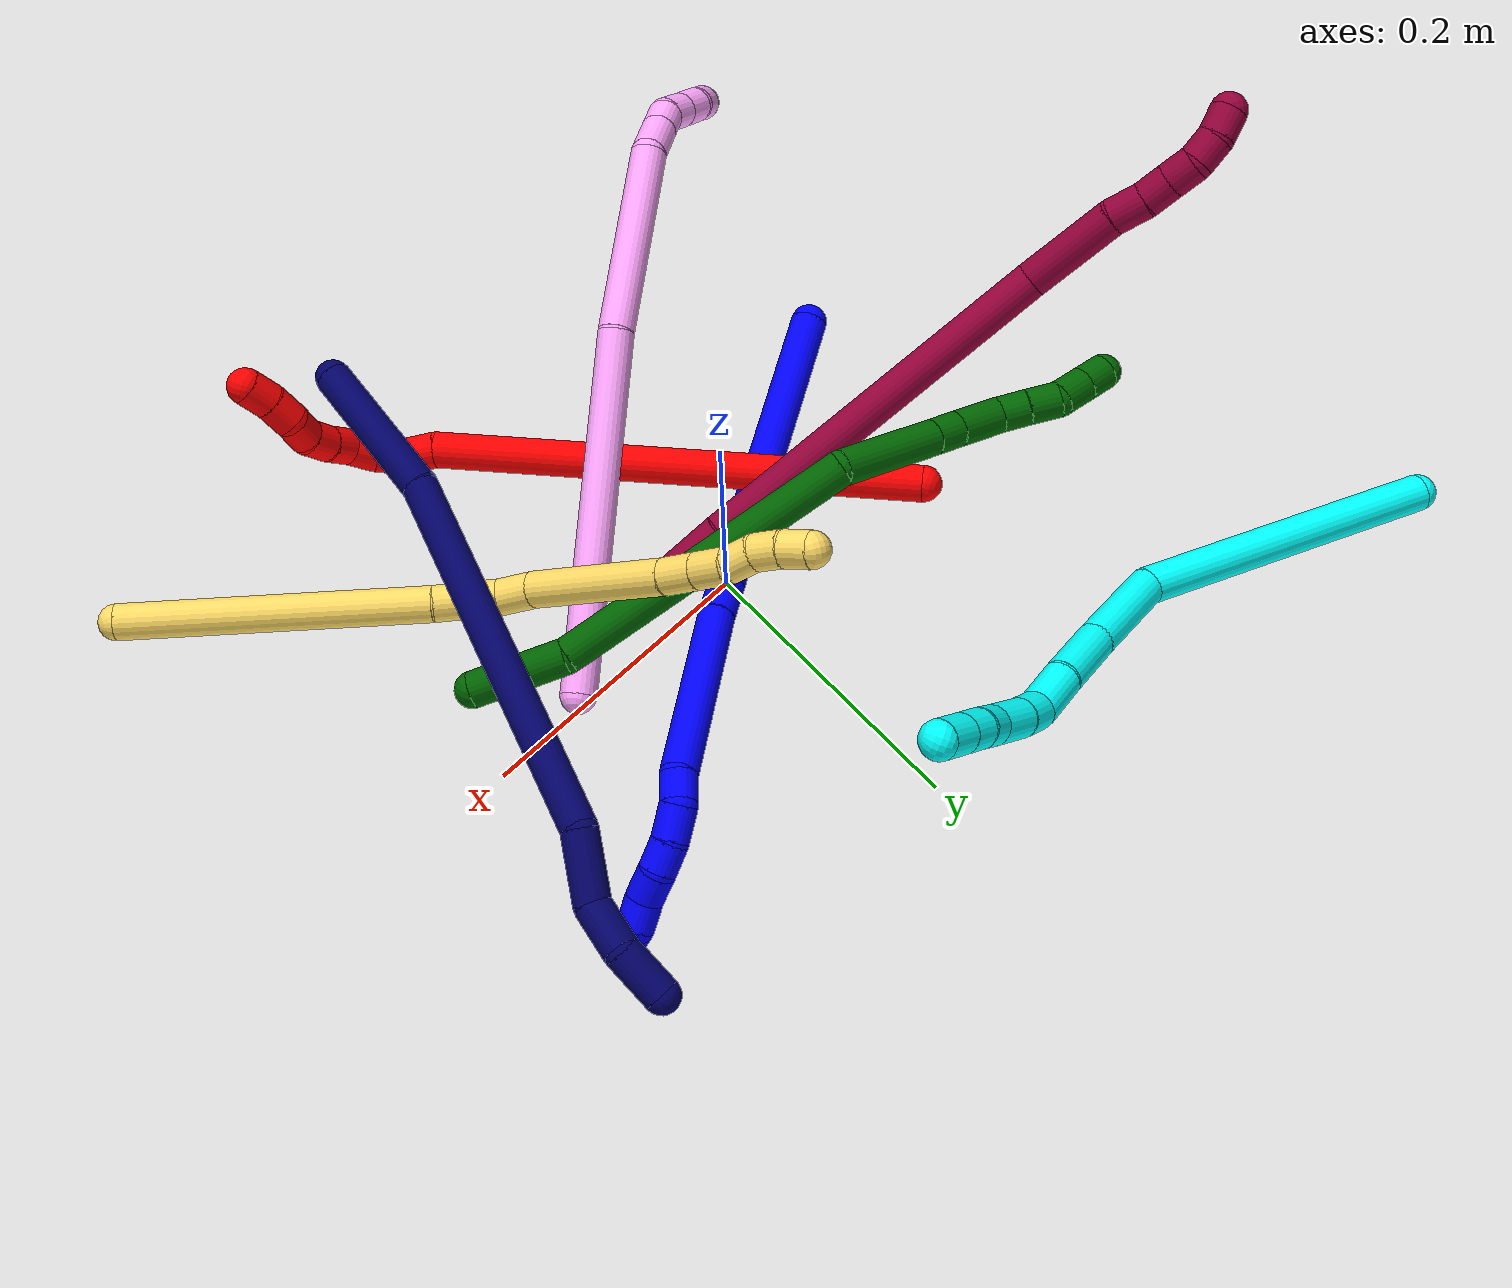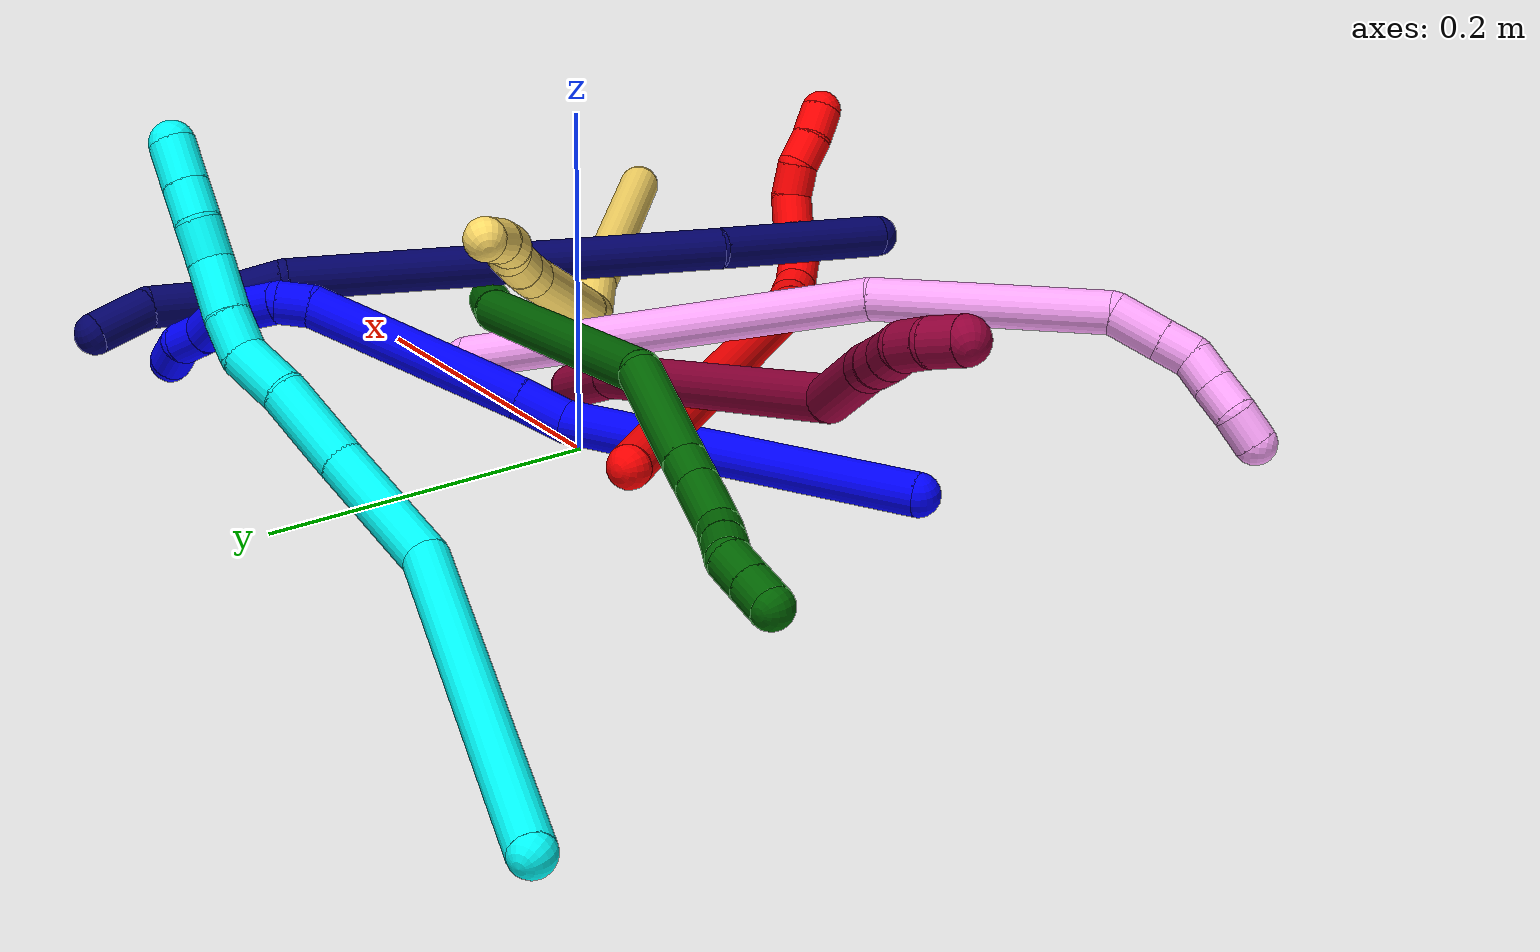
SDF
<sdf version="1.7">
 <world name="default">
  <plugin name="TubeGeneratorPlugin" filename="libtube_generator_plugin.so"/>
  <model name="photoneo_s_sensor">
   <static>1</static>
   <pose>0 0 2 1.57079 1.57079 3.14159</pose>
   <link name="link">
    <inertial><mass>0.1</mass></inertial>
    <sensor name="sensor" type="depth">
     <update_rate>30</update_rate>
     <camera>
      <horizontal_fov>1.22</horizontal_fov>
      <image><width>1920</width><height>1200</height><format>B8G8R8</format></image>
      <clip><near>0.1</near><far>4</far></clip>
      <depth_camera><output>points</output></depth_camera>
     </camera>
     <plugin name="camera_plugin" filename="libgazebo_ros_depth_camera.so">
      <baseline>0.2</baseline>
      <alwaysOn>1</alwaysOn>
      <updateRate>0.0</updateRate>
      <cameraName>camera_ir</cameraName>
      <imageTopicName>/camera/color/image_raw</imageTopicName>
      <cameraInfoTopicName>/camera/color/camera_info</cameraInfoTopicName>
      <depthImageTopicName>/camera/depth/image_raw</depthImageTopicName>
      <depthImageCameraInfoTopicName>/camera/depth/camera_info</depthImageCameraInfoTopicName>
      <pointCloudTopicName>/camera/depth/points</pointCloudTopicName>
      <frameName>fr_optical</frameName>
      <pointCloudCutoff>0.1</pointCloudCutoff>
      <pointCloudCutoffMax>2.0</pointCloudCutoffMax>
      <distortionK1>0</distortionK1>
      <distortionK2>0</distortionK2>
      <distortionK3>0</distortionK3>
      <distortionT1>0</distortionT1>
      <distortionT2>0</distortionT2>
      <CxPrime>0</CxPrime>
      <Cx>0</Cx>
      <Cy>0</Cy>
      <focalLength>0</focalLength>
      <hackBaseline>0</hackBaseline>
     </plugin>
    </sensor>
   </link>
  </model>
  <gravity>0 0 -9.8</gravity>
  <magnetic_field>6e-06 2.3e-05 -4.2e-05</magnetic_field>
  <atmosphere type="adiabatic"/>
  <physics name="default_physics" default="0" type="ode">
   <max_step_size>0.003</max_step_size>
   <real_time_factor>1</real_time_factor>
   <real_time_update_rate>1000</real_time_update_rate>
   <max_contacts>10000</max_contacts>
   <ode>
    <solver>
     <type>quick</type>
     <iters>100</iters>
     <sor>1.3</sor>
     <use_dynamic_moi_rescaling>0</use_dynamic_moi_rescaling>
    </solver>
    <constraints>
     <contact_max_correcting_vel>0</contact_max_correcting_vel>
     <contact_surface_layer>0.001</contact_surface_layer>
     <cfm>0</cfm>
     <erp>0.2</erp>
    </constraints>
   </ode>
  </physics>
  <scene><ambient>0.4 0.4 0.4 1</ambient><background>0.7 0.7 0.7 1</background><shadows>0</shadows></scene>
  <audio><device>default</device></audio>
  <spherical_coordinates>
   <surface_model>EARTH_WGS84</surface_model>
   <latitude_deg>0</latitude_deg>
   <longitude_deg>0</longitude_deg>
   <elevation>0</elevation>
   <heading_deg>0</heading_deg>
  </spherical_coordinates>
  <model name="bin">
   <static>1</static>
   <link name="bottom">
    <collision name="collision-bottom">
     <pose>0 0 -0.01 0 -0 0</pose>
     <geometry><box><size>0.8 0.6 0.02</size></box></geometry>
     <surface>
      <friction><ode><mu>100</mu><mu2>100</mu2></ode></friction>
      <contact><collide_bitmask>65535</collide_bitmask></contact>
     </surface>
    </collision>
   </link>
   <link name="west_wall">
    <collision name="collision-west_wall">
     <pose>-0.41 0 0.1 0 -0 0</pose>
     <geometry><box><size>0.02 0.6 0.2</size></box></geometry>
     <surface>
      <friction><ode><mu>100</mu><mu2>100</mu2></ode></friction>
      <contact><collide_bitmask>65535</collide_bitmask></contact>
     </surface>
    </collision>
   </link>
   <link name="east_wall">
    <collision name="collision-east_wall">
     <pose>0.41 0 0.1 0 -0 0</pose>
     <geometry><box><size>0.02 0.6 0.2</size></box></geometry>
     <surface>
      <friction><ode><mu>100</mu><mu2>100</mu2></ode></friction>
      <contact><collide_bitmask>65535</collide_bitmask></contact>
     </surface>
    </collision>
   </link>
   <link name="south_wall">
    <collision name="collision-south_wall">
     <pose>0 -0.31 0.1 0 -0 0</pose>
     <geometry><box><size>0.8 0.02 0.2</size></box></geometry>
     <surface>
      <friction><ode><mu>100</mu><mu2>100</mu2></ode></friction>
      <contact><collide_bitmask>65535</collide_bitmask></contact>
     </surface>
    </collision>
   </link>
   <link name="north_wall">
    <collision name="collision-north_wall">
     <pose>0 0.31 0.1 0 -0 0</pose>
     <geometry><box><size>0.8 0.02 0.2</size></box></geometry>
     <surface>
      <friction><ode><mu>100</mu><mu2>100</mu2></ode></friction>
      <contact><collide_bitmask>65535</collide_bitmask></contact>
     </surface>
    </collision>
   </link>
  </model>
  <model name="1">
   <static>0</static>
   <link name="1">
    <collision name="collision-cylinder-e_1_1_4">
     <pose>0.093026 0.051298 0.000636 -1.55841 1.06681 -1.056</pose>
     <geometry><cylinder><radius>0.0125</radius><length>0.212468</length></cylinder></geometry>
     <surface>
      <friction><ode><mu>1.16</mu><mu2>1.16</mu2><slip1>0</slip1><slip2>0</slip2></ode></friction>
      <contact><ode><kp>1e+06</kp><kd>1</kd><max_vel>0</max_vel><min_depth>0.001</min_depth></ode></contact>
     </surface>
    </collision>
    <visual name="visual-cylinder-e_1_1_4">
     <pose>0.093026 0.051298 0.000636 -1.55841 1.06681 -1.056</pose>
     <geometry><cylinder><radius>0.0125</radius><length>0.212468</length></cylinder></geometry>
     <material><ambient>0 0 1 1</ambient></material>
    </visual>
    <collision name="collision-cylinder-e_2_4_5">
     <pose>0.198539 0.109345 0.005745 -0.985389 0.995567 -0.567726</pose>
     <geometry><cylinder><radius>0.0125</radius><length>0.029766</length></cylinder></geometry>
     <surface>
      <friction><ode><mu>1.16</mu><mu2>1.16</mu2><slip1>0</slip1><slip2>0</slip2></ode></friction>
      <contact><ode><kp>1e+06</kp><kd>1</kd><max_vel>0</max_vel><min_depth>0.001</min_depth></ode></contact>
     </surface>
    </collision>
    <visual name="visual-cylinder-e_2_4_5">
     <pose>0.198539 0.109345 0.005745 -0.985389 0.995567 -0.567726</pose>
     <geometry><cylinder><radius>0.0125</radius><length>0.029766</length></cylinder></geometry>
     <material><ambient>0 0 1 1</ambient></material>
    </visual>
    <collision name="collision-cylinder-e_3_5_6">
     <pose>0.264823 0.149482 0.029846 -1.03937 0.946814 -0.570201</pose>
     <geometry><cylinder><radius>0.0125</radius><length>0.132576</length></cylinder></geometry>
     <surface>
      <friction><ode><mu>1.16</mu><mu2>1.16</mu2><slip1>0</slip1><slip2>0</slip2></ode></friction>
      <contact><ode><kp>1e+06</kp><kd>1</kd><max_vel>0</max_vel><min_depth>0.001</min_depth></ode></contact>
     </surface>
    </collision>
    <visual name="visual-cylinder-e_3_5_6">
     <pose>0.264823 0.149482 0.029846 -1.03937 0.946814 -0.570201</pose>
     <geometry><cylinder><radius>0.0125</radius><length>0.132576</length></cylinder></geometry>
     <material><ambient>0 0 1 1</ambient></material>
    </visual>
    <collision name="collision-cylinder-e_4_6_7">
     <pose>0.325707 0.189912 0.050444 -1.43371 0.783941 -0.691554</pose>
     <geometry><cylinder><radius>0.0125</radius><length>0.020074</length></cylinder></geometry>
     <surface>
      <friction><ode><mu>1.16</mu><mu2>1.16</mu2><slip1>0</slip1><slip2>0</slip2></ode></friction>
      <contact><ode><kp>1e+06</kp><kd>1</kd><max_vel>0</max_vel><min_depth>0.001</min_depth></ode></contact>
     </surface>
    </collision>
    <visual name="visual-cylinder-e_4_6_7">
     <pose>0.325707 0.189912 0.050444 -1.43371 0.783941 -0.691554</pose>
     <geometry><cylinder><radius>0.0125</radius><length>0.020074</length></cylinder></geometry>
     <material><ambient>0 0 1 1</ambient></material>
    </visual>
    <collision name="collision-cylinder-e_5_7_8">
     <pose>0.342015 0.203012 0.047442 -2.15122 0.904744 -1.46547</pose>
     <geometry><cylinder><radius>0.0125</radius><length>0.023455</length></cylinder></geometry>
     <surface>
      <friction><ode><mu>1.16</mu><mu2>1.16</mu2><slip1>0</slip1><slip2>0</slip2></ode></friction>
      <contact><ode><kp>1e+06</kp><kd>1</kd><max_vel>0</max_vel><min_depth>0.001</min_depth></ode></contact>
     </surface>
    </collision>
    <visual name="visual-cylinder-e_5_7_8">
     <pose>0.342015 0.203012 0.047442 -2.15122 0.904744 -1.46547</pose>
     <geometry><cylinder><radius>0.0125</radius><length>0.023455</length></cylinder></geometry>
     <material><ambient>0 0 1 1</ambient></material>
    </visual>
    <collision name="collision-cylinder-e_6_8_9">
     <pose>0.359433 0.21263 0.038614 -2.50909 0.937452 -1.99413</pose>
     <geometry><cylinder><radius>0.0125</radius><length>0.02034</length></cylinder></geometry>
     <surface>
      <friction><ode><mu>1.16</mu><mu2>1.16</mu2><slip1>0</slip1><slip2>0</slip2></ode></friction>
      <contact><ode><kp>1e+06</kp><kd>1</kd><max_vel>0</max_vel><min_depth>0.001</min_depth></ode></contact>
     </surface>
    </collision>
    <visual name="visual-cylinder-e_6_8_9">
     <pose>0.359433 0.21263 0.038614 -2.50909 0.937452 -1.99413</pose>
     <geometry><cylinder><radius>0.0125</radius><length>0.02034</length></cylinder></geometry>
     <material><ambient>0 0 1 1</ambient></material>
    </visual>
    <collision name="collision-cylinder-e_7_9_10">
     <pose>0.374568 0.218777 0.026162 -2.81322 0.712842 -2.30424</pose>
     <geometry><cylinder><radius>0.0125</radius><length>0.021217</length></cylinder></geometry>
     <surface>
      <friction><ode><mu>1.16</mu><mu2>1.16</mu2><slip1>0</slip1><slip2>0</slip2></ode></friction>
      <contact><ode><kp>1e+06</kp><kd>1</kd><max_vel>0</max_vel><min_depth>0.001</min_depth></ode></contact>
     </surface>
    </collision>
    <visual name="visual-cylinder-e_7_9_10">
     <pose>0.374568 0.218777 0.026162 -2.81322 0.712842 -2.30424</pose>
     <geometry><cylinder><radius>0.0125</radius><length>0.021217</length></cylinder></geometry>
     <material><ambient>0 0 1 1</ambient></material>
    </visual>
    <collision name="collision-cylinder-e_8_10_11">
     <pose>0.388923 0.225504 0.013283 -2.47703 0.835272 -1.81967</pose>
     <geometry><cylinder><radius>0.0125</radius><length>0.020004</length></cylinder></geometry>
     <surface>
      <friction><ode><mu>1.16</mu><mu2>1.16</mu2><slip1>0</slip1><slip2>0</slip2></ode></friction>
      <contact><ode><kp>1e+06</kp><kd>1</kd><max_vel>0</max_vel><min_depth>0.001</min_depth></ode></contact>
     </surface>
    </collision>
    <visual name="visual-cylinder-e_8_10_11">
     <pose>0.388923 0.225504 0.013283 -2.47703 0.835272 -1.81967</pose>
     <geometry><cylinder><radius>0.0125</radius><length>0.020004</length></cylinder></geometry>
     <material><ambient>0 0 1 1</ambient></material>
    </visual>
    <collision name="collision-cylinder-e_9_11_2">
     <pose>0.402218 0.230643 -9e-05 -3.0186 0.624836 -2.76486</pose>
     <geometry><cylinder><radius>0.0125</radius><length>0.0201</length></cylinder></geometry>
     <surface>
      <friction><ode><mu>1.16</mu><mu2>1.16</mu2><slip1>0</slip1><slip2>0</slip2></ode></friction>
      <contact><ode><kp>1e+06</kp><kd>1</kd><max_vel>0</max_vel><min_depth>0.001</min_depth></ode></contact>
     </surface>
    </collision>
    <visual name="visual-cylinder-e_9_11_2">
     <pose>0.402218 0.230643 -9e-05 -3.0186 0.624836 -2.76486</pose>
     <geometry><cylinder><radius>0.0125</radius><length>0.0201</length></cylinder></geometry>
     <material><ambient>0 0 1 1</ambient></material>
    </visual>
    <collision name="collision-sphere-2">
     <pose>0.408097 0.231642 -0.008179 0 -0 0</pose>
     <geometry><sphere><radius>0.0125</radius></sphere></geometry>
     <surface>
      <friction><ode><mu>1.16</mu><mu2>1.16</mu2><slip1>0</slip1><slip2>0</slip2></ode></friction>
      <contact><ode><kp>1e+06</kp><kd>1</kd><max_vel>0</max_vel><min_depth>0.001</min_depth></ode></contact>
     </surface>
    </collision>
    <visual name="visual-sphere-2">
     <pose>0.408097 0.231642 -0.008179 0 -0 0</pose>
     <geometry><sphere><radius>0.0125</radius></sphere></geometry>
     <material><ambient>0 0 1 1</ambient></material>
    </visual>
    <collision name="collision-sphere-11">
     <pose>0.396339 0.229643 0.008 0 -0 0</pose>
     <geometry><sphere><radius>0.0125</radius></sphere></geometry>
     <surface>
      <friction><ode><mu>1.16</mu><mu2>1.16</mu2><slip1>0</slip1><slip2>0</slip2></ode></friction>
      <contact><ode><kp>1e+06</kp><kd>1</kd><max_vel>0</max_vel><min_depth>0.001</min_depth></ode></contact>
     </surface>
    </collision>
    <visual name="visual-sphere-11">
     <pose>0.396339 0.229643 0.008 0 -0 0</pose>
     <geometry><sphere><radius>0.0125</radius></sphere></geometry>
     <material><ambient>0 0 1 1</ambient></material>
    </visual>
    <collision name="collision-sphere-10">
     <pose>0.381506 0.221365 0.018566 0 -0 0</pose>
     <geometry><sphere><radius>0.0125</radius></sphere></geometry>
     <surface>
      <friction><ode><mu>1.16</mu><mu2>1.16</mu2><slip1>0</slip1><slip2>0</slip2></ode></friction>
      <contact><ode><kp>1e+06</kp><kd>1</kd><max_vel>0</max_vel><min_depth>0.001</min_depth></ode></contact>
     </surface>
    </collision>
    <visual name="visual-sphere-10">
     <pose>0.381506 0.221365 0.018566 0 -0 0</pose>
     <geometry><sphere><radius>0.0125</radius></sphere></geometry>
     <material><ambient>0 0 1 1</ambient></material>
    </visual>
    <collision name="collision-sphere-9">
     <pose>0.36763 0.216188 0.033759 0 -0 0</pose>
     <geometry><sphere><radius>0.0125</radius></sphere></geometry>
     <surface>
      <friction><ode><mu>1.16</mu><mu2>1.16</mu2><slip1>0</slip1><slip2>0</slip2></ode></friction>
      <contact><ode><kp>1e+06</kp><kd>1</kd><max_vel>0</max_vel><min_depth>0.001</min_depth></ode></contact>
     </surface>
    </collision>
    <visual name="visual-sphere-9">
     <pose>0.36763 0.216188 0.033759 0 -0 0</pose>
     <geometry><sphere><radius>0.0125</radius></sphere></geometry>
     <material><ambient>0 0 1 1</ambient></material>
    </visual>
    <collision name="collision-sphere-4">
     <pose>0.186051 0.102597 0.001271 0 -0 0</pose>
     <geometry><sphere><radius>0.0125</radius></sphere></geometry>
     <surface>
      <friction><ode><mu>1.16</mu><mu2>1.16</mu2><slip1>0</slip1><slip2>0</slip2></ode></friction>
      <contact><ode><kp>1e+06</kp><kd>1</kd><max_vel>0</max_vel><min_depth>0.001</min_depth></ode></contact>
     </surface>
    </collision>
    <visual name="visual-sphere-4">
     <pose>0.186051 0.102597 0.001271 0 -0 0</pose>
     <geometry><sphere><radius>0.0125</radius></sphere></geometry>
     <material><ambient>0 0 1 1</ambient></material>
    </visual>
    <collision name="collision-sphere-1">
     <geometry><sphere><radius>0.0125</radius></sphere></geometry>
     <surface>
      <friction><ode><mu>1.16</mu><mu2>1.16</mu2><slip1>0</slip1><slip2>0</slip2></ode></friction>
      <contact><ode><kp>1e+06</kp><kd>1</kd><max_vel>0</max_vel><min_depth>0.001</min_depth></ode></contact>
     </surface>
    </collision>
    <visual name="visual-sphere-1">
     <geometry><sphere><radius>0.0125</radius></sphere></geometry>
     <material><ambient>0 0 1 1</ambient></material>
    </visual>
    <collision name="collision-sphere-8">
     <pose>0.351236 0.209072 0.043468 0 -0 0</pose>
     <geometry><sphere><radius>0.0125</radius></sphere></geometry>
     <surface>
      <friction><ode><mu>1.16</mu><mu2>1.16</mu2><slip1>0</slip1><slip2>0</slip2></ode></friction>
      <contact><ode><kp>1e+06</kp><kd>1</kd><max_vel>0</max_vel><min_depth>0.001</min_depth></ode></contact>
     </surface>
    </collision>
    <visual name="visual-sphere-8">
     <pose>0.351236 0.209072 0.043468 0 -0 0</pose>
     <geometry><sphere><radius>0.0125</radius></sphere></geometry>
     <material><ambient>0 0 1 1</ambient></material>
    </visual>
    <collision name="collision-sphere-5">
     <pose>0.211027 0.116094 0.010219 0 -0 0</pose>
     <geometry><sphere><radius>0.0125</radius></sphere></geometry>
     <surface>
      <friction><ode><mu>1.16</mu><mu2>1.16</mu2><slip1>0</slip1><slip2>0</slip2></ode></friction>
      <contact><ode><kp>1e+06</kp><kd>1</kd><max_vel>0</max_vel><min_depth>0.001</min_depth></ode></contact>
     </surface>
    </collision>
    <visual name="visual-sphere-5">
     <pose>0.211027 0.116094 0.010219 0 -0 0</pose>
     <geometry><sphere><radius>0.0125</radius></sphere></geometry>
     <material><ambient>0 0 1 1</ambient></material>
    </visual>
    <collision name="collision-sphere-6">
     <pose>0.31862 0.182871 0.049473 0 -0 0</pose>
     <geometry><sphere><radius>0.0125</radius></sphere></geometry>
     <surface>
      <friction><ode><mu>1.16</mu><mu2>1.16</mu2><slip1>0</slip1><slip2>0</slip2></ode></friction>
      <contact><ode><kp>1e+06</kp><kd>1</kd><max_vel>0</max_vel><min_depth>0.001</min_depth></ode></contact>
     </surface>
    </collision>
    <visual name="visual-sphere-6">
     <pose>0.31862 0.182871 0.049473 0 -0 0</pose>
     <geometry><sphere><radius>0.0125</radius></sphere></geometry>
     <material><ambient>0 0 1 1</ambient></material>
    </visual>
    <collision name="collision-sphere-7">
     <pose>0.332794 0.196953 0.051416 0 -0 0</pose>
     <geometry><sphere><radius>0.0125</radius></sphere></geometry>
     <surface>
      <friction><ode><mu>1.16</mu><mu2>1.16</mu2><slip1>0</slip1><slip2>0</slip2></ode></friction>
      <contact><ode><kp>1e+06</kp><kd>1</kd><max_vel>0</max_vel><min_depth>0.001</min_depth></ode></contact>
     </surface>
    </collision>
    <visual name="visual-sphere-7">
     <pose>0.332794 0.196953 0.051416 0 -0 0</pose>
     <geometry><sphere><radius>0.0125</radius></sphere></geometry>
     <material><ambient>0 0 1 1</ambient></material>
    </visual>
    <inertial>
     <pose>0.212933 0.121319 0.015985 0 -0 0</pose>
     <mass>0.5</mass>
     <inertia>
      <ixx>-8.6e-05</ixx>
      <ixy>0</ixy>
      <ixz>0</ixz>
      <iyy>0.0004</iyy>
      <iyz>0</iyz>
      <izz>-0.001375</izz>
     </inertia>
    </inertial>
   </link>
   <pose>-0.176869 -0.104028 0.01149 -0.129202 -0.092745 0.042245</pose>
  </model>
  <model name="2">
   <static>0</static>
   <link name="2">
    <collision name="collision-cylinder-e_1_1_4">
     <pose>0.007255 -0.048314 0.161573 0.290561 0.042992 0.006291</pose>
     <geometry><cylinder><radius>0.0125</radius><length>0.337596</length></cylinder></geometry>
     <surface>
      <friction><ode><mu>1.16</mu><mu2>1.16</mu2><slip1>0</slip1><slip2>0</slip2></ode></friction>
      <contact><ode><kp>1e+06</kp><kd>1</kd><max_vel>0</max_vel><min_depth>0.001</min_depth></ode></contact>
     </surface>
    </collision>
    <visual name="visual-cylinder-e_1_1_4">
     <pose>0.007255 -0.048314 0.161573 0.290561 0.042992 0.006291</pose>
     <geometry><cylinder><radius>0.0125</radius><length>0.337596</length></cylinder></geometry>
     <material><ambient>1 0 0 1</ambient></material>
    </visual>
    <collision name="collision-cylinder-e_2_4_5">
     <pose>0.014429 -0.102456 0.331988 0.582765 -0.007633 -0.002289</pose>
     <geometry><cylinder><radius>0.0125</radius><length>0.021178</length></cylinder></geometry>
     <surface>
      <friction><ode><mu>1.16</mu><mu2>1.16</mu2><slip1>0</slip1><slip2>0</slip2></ode></friction>
      <contact><ode><kp>1e+06</kp><kd>1</kd><max_vel>0</max_vel><min_depth>0.001</min_depth></ode></contact>
     </surface>
    </collision>
    <visual name="visual-cylinder-e_2_4_5">
     <pose>0.014429 -0.102456 0.331988 0.582765 -0.007633 -0.002289</pose>
     <geometry><cylinder><radius>0.0125</radius><length>0.021178</length></cylinder></geometry>
     <material><ambient>1 0 0 1</ambient></material>
    </visual>
    <collision name="collision-cylinder-e_3_5_6">
     <pose>0.016499 -0.11182 0.350167 0.362 0.212154 0.038966</pose>
     <geometry><cylinder><radius>0.0125</radius><length>0.02043</length></cylinder></geometry>
     <surface>
      <friction><ode><mu>1.16</mu><mu2>1.16</mu2><slip1>0</slip1><slip2>0</slip2></ode></friction>
      <contact><ode><kp>1e+06</kp><kd>1</kd><max_vel>0</max_vel><min_depth>0.001</min_depth></ode></contact>
     </surface>
    </collision>
    <visual name="visual-cylinder-e_3_5_6">
     <pose>0.016499 -0.11182 0.350167 0.362 0.212154 0.038966</pose>
     <geometry><cylinder><radius>0.0125</radius><length>0.02043</length></cylinder></geometry>
     <material><ambient>1 0 0 1</ambient></material>
    </visual>
    <collision name="collision-cylinder-e_4_6_7">
     <pose>0.025482 -0.118273 0.366738 0.383395 0.7195 0.145736</pose>
     <geometry><cylinder><radius>0.0125</radius><length>0.020735</length></cylinder></geometry>
     <surface>
      <friction><ode><mu>1.16</mu><mu2>1.16</mu2><slip1>0</slip1><slip2>0</slip2></ode></friction>
      <contact><ode><kp>1e+06</kp><kd>1</kd><max_vel>0</max_vel><min_depth>0.001</min_depth></ode></contact>
     </surface>
    </collision>
    <visual name="visual-cylinder-e_4_6_7">
     <pose>0.025482 -0.118273 0.366738 0.383395 0.7195 0.145736</pose>
     <geometry><cylinder><radius>0.0125</radius><length>0.020735</length></cylinder></geometry>
     <material><ambient>1 0 0 1</ambient></material>
    </visual>
    <collision name="collision-cylinder-e_5_7_8">
     <pose>0.040792 -0.125431 0.377166 0.924945 1.01118 0.53855</pose>
     <geometry><cylinder><radius>0.0125</radius><length>0.020006</length></cylinder></geometry>
     <surface>
      <friction><ode><mu>1.16</mu><mu2>1.16</mu2><slip1>0</slip1><slip2>0</slip2></ode></friction>
      <contact><ode><kp>1e+06</kp><kd>1</kd><max_vel>0</max_vel><min_depth>0.001</min_depth></ode></contact>
     </surface>
    </collision>
    <visual name="visual-cylinder-e_5_7_8">
     <pose>0.040792 -0.125431 0.377166 0.924945 1.01118 0.53855</pose>
     <geometry><cylinder><radius>0.0125</radius><length>0.020006</length></cylinder></geometry>
     <material><ambient>1 0 0 1</ambient></material>
    </visual>
    <collision name="collision-cylinder-e_6_8_9">
     <pose>0.058196 -0.13262 0.383788 0.710652 1.10214 0.448442</pose>
     <geometry><cylinder><radius>0.0125</radius><length>0.020013</length></cylinder></geometry>
     <surface>
      <friction><ode><mu>1.16</mu><mu2>1.16</mu2><slip1>0</slip1><slip2>0</slip2></ode></friction>
      <contact><ode><kp>1e+06</kp><kd>1</kd><max_vel>0</max_vel><min_depth>0.001</min_depth></ode></contact>
     </surface>
    </collision>
    <visual name="visual-cylinder-e_6_8_9">
     <pose>0.058196 -0.13262 0.383788 0.710652 1.10214 0.448442</pose>
     <geometry><cylinder><radius>0.0125</radius><length>0.020013</length></cylinder></geometry>
     <material><ambient>1 0 0 1</ambient></material>
    </visual>
    <collision name="collision-cylinder-e_7_9_10">
     <pose>0.076742 -0.134965 0.389942 -0.217541 1.28797 -0.163602</pose>
     <geometry><cylinder><radius>0.0125</radius><length>0.020032</length></cylinder></geometry>
     <surface>
      <friction><ode><mu>1.16</mu><mu2>1.16</mu2><slip1>0</slip1><slip2>0</slip2></ode></friction>
      <contact><ode><kp>1e+06</kp><kd>1</kd><max_vel>0</max_vel><min_depth>0.001</min_depth></ode></contact>
     </surface>
    </collision>
    <visual name="visual-cylinder-e_7_9_10">
     <pose>0.076742 -0.134965 0.389942 -0.217541 1.28797 -0.163602</pose>
     <geometry><cylinder><radius>0.0125</radius><length>0.020032</length></cylinder></geometry>
     <material><ambient>1 0 0 1</ambient></material>
    </visual>
    <collision name="collision-cylinder-e_8_10_11">
     <pose>0.094232 -0.133085 0.398705 -0.208584 0.906252 -0.101845</pose>
     <geometry><cylinder><radius>0.0125</radius><length>0.020002</length></cylinder></geometry>
     <surface>
      <friction><ode><mu>1.16</mu><mu2>1.16</mu2><slip1>0</slip1><slip2>0</slip2></ode></friction>
      <contact><ode><kp>1e+06</kp><kd>1</kd><max_vel>0</max_vel><min_depth>0.001</min_depth></ode></contact>
     </surface>
    </collision>
    <visual name="visual-cylinder-e_8_10_11">
     <pose>0.094232 -0.133085 0.398705 -0.208584 0.906252 -0.101845</pose>
     <geometry><cylinder><radius>0.0125</radius><length>0.020002</length></cylinder></geometry>
     <material><ambient>1 0 0 1</ambient></material>
    </visual>
    <collision name="collision-cylinder-e_9_11_2">
     <pose>0.10987 -0.132155 0.411037 0.055144 0.888665 0.026258</pose>
     <geometry><cylinder><radius>0.0125</radius><length>0.020008</length></cylinder></geometry>
     <surface>
      <friction><ode><mu>1.16</mu><mu2>1.16</mu2><slip1>0</slip1><slip2>0</slip2></ode></friction>
      <contact><ode><kp>1e+06</kp><kd>1</kd><max_vel>0</max_vel><min_depth>0.001</min_depth></ode></contact>
     </surface>
    </collision>
    <visual name="visual-cylinder-e_9_11_2">
     <pose>0.10987 -0.132155 0.411037 0.055144 0.888665 0.026258</pose>
     <geometry><cylinder><radius>0.0125</radius><length>0.020008</length></cylinder></geometry>
     <material><ambient>1 0 0 1</ambient></material>
    </visual>
    <collision name="collision-sphere-2">
     <pose>0.117636 -0.132503 0.417334 0 -0 0</pose>
     <geometry><sphere><radius>0.0125</radius></sphere></geometry>
     <surface>
      <friction><ode><mu>1.16</mu><mu2>1.16</mu2><slip1>0</slip1><slip2>0</slip2></ode></friction>
      <contact><ode><kp>1e+06</kp><kd>1</kd><max_vel>0</max_vel><min_depth>0.001</min_depth></ode></contact>
     </surface>
    </collision>
    <visual name="visual-sphere-2">
     <pose>0.117636 -0.132503 0.417334 0 -0 0</pose>
     <geometry><sphere><radius>0.0125</radius></sphere></geometry>
     <material><ambient>1 0 0 1</ambient></material>
    </visual>
    <collision name="collision-sphere-11">
     <pose>0.102105 -0.131807 0.404739 0 -0 0</pose>
     <geometry><sphere><radius>0.0125</radius></sphere></geometry>
     <surface>
      <friction><ode><mu>1.16</mu><mu2>1.16</mu2><slip1>0</slip1><slip2>0</slip2></ode></friction>
      <contact><ode><kp>1e+06</kp><kd>1</kd><max_vel>0</max_vel><min_depth>0.001</min_depth></ode></contact>
     </surface>
    </collision>
    <visual name="visual-sphere-11">
     <pose>0.102105 -0.131807 0.404739 0 -0 0</pose>
     <geometry><sphere><radius>0.0125</radius></sphere></geometry>
     <material><ambient>1 0 0 1</ambient></material>
    </visual>
    <collision name="collision-sphere-10">
     <pose>0.08636 -0.134362 0.392672 0 -0 0</pose>
     <geometry><sphere><radius>0.0125</radius></sphere></geometry>
     <surface>
      <friction><ode><mu>1.16</mu><mu2>1.16</mu2><slip1>0</slip1><slip2>0</slip2></ode></friction>
      <contact><ode><kp>1e+06</kp><kd>1</kd><max_vel>0</max_vel><min_depth>0.001</min_depth></ode></contact>
     </surface>
    </collision>
    <visual name="visual-sphere-10">
     <pose>0.08636 -0.134362 0.392672 0 -0 0</pose>
     <geometry><sphere><radius>0.0125</radius></sphere></geometry>
     <material><ambient>1 0 0 1</ambient></material>
    </visual>
    <collision name="collision-sphere-9">
     <pose>0.067124 -0.135568 0.387213 0 -0 0</pose>
     <geometry><sphere><radius>0.0125</radius></sphere></geometry>
     <surface>
      <friction><ode><mu>1.16</mu><mu2>1.16</mu2><slip1>0</slip1><slip2>0</slip2></ode></friction>
      <contact><ode><kp>1e+06</kp><kd>1</kd><max_vel>0</max_vel><min_depth>0.001</min_depth></ode></contact>
     </surface>
    </collision>
    <visual name="visual-sphere-9">
     <pose>0.067124 -0.135568 0.387213 0 -0 0</pose>
     <geometry><sphere><radius>0.0125</radius></sphere></geometry>
     <material><ambient>1 0 0 1</ambient></material>
    </visual>
    <collision name="collision-sphere-4">
     <pose>0.01451 -0.096629 0.323147 0 -0 0</pose>
     <geometry><sphere><radius>0.0125</radius></sphere></geometry>
     <surface>
      <friction><ode><mu>1.16</mu><mu2>1.16</mu2><slip1>0</slip1><slip2>0</slip2></ode></friction>
      <contact><ode><kp>1e+06</kp><kd>1</kd><max_vel>0</max_vel><min_depth>0.001</min_depth></ode></contact>
     </surface>
    </collision>
    <visual name="visual-sphere-4">
     <pose>0.01451 -0.096629 0.323147 0 -0 0</pose>
     <geometry><sphere><radius>0.0125</radius></sphere></geometry>
     <material><ambient>1 0 0 1</ambient></material>
    </visual>
    <collision name="collision-sphere-1">
     <geometry><sphere><radius>0.0125</radius></sphere></geometry>
     <surface>
      <friction><ode><mu>1.16</mu><mu2>1.16</mu2><slip1>0</slip1><slip2>0</slip2></ode></friction>
      <contact><ode><kp>1e+06</kp><kd>1</kd><max_vel>0</max_vel><min_depth>0.001</min_depth></ode></contact>
     </surface>
    </collision>
    <visual name="visual-sphere-1">
     <geometry><sphere><radius>0.0125</radius></sphere></geometry>
     <material><ambient>1 0 0 1</ambient></material>
    </visual>
    <collision name="collision-sphere-8">
     <pose>0.049269 -0.129672 0.380362 0 -0 0</pose>
     <geometry><sphere><radius>0.0125</radius></sphere></geometry>
     <surface>
      <friction><ode><mu>1.16</mu><mu2>1.16</mu2><slip1>0</slip1><slip2>0</slip2></ode></friction>
      <contact><ode><kp>1e+06</kp><kd>1</kd><max_vel>0</max_vel><min_depth>0.001</min_depth></ode></contact>
     </surface>
    </collision>
    <visual name="visual-sphere-8">
     <pose>0.049269 -0.129672 0.380362 0 -0 0</pose>
     <geometry><sphere><radius>0.0125</radius></sphere></geometry>
     <material><ambient>1 0 0 1</ambient></material>
    </visual>
    <collision name="collision-sphere-5">
     <pose>0.014348 -0.108283 0.340829 0 -0 0</pose>
     <geometry><sphere><radius>0.0125</radius></sphere></geometry>
     <surface>
      <friction><ode><mu>1.16</mu><mu2>1.16</mu2><slip1>0</slip1><slip2>0</slip2></ode></friction>
      <contact><ode><kp>1e+06</kp><kd>1</kd><max_vel>0</max_vel><min_depth>0.001</min_depth></ode></contact>
     </surface>
    </collision>
    <visual name="visual-sphere-5">
     <pose>0.014348 -0.108283 0.340829 0 -0 0</pose>
     <geometry><sphere><radius>0.0125</radius></sphere></geometry>
     <material><ambient>1 0 0 1</ambient></material>
    </visual>
    <collision name="collision-sphere-6">
     <pose>0.01865 -0.115356 0.359506 0 -0 0</pose>
     <geometry><sphere><radius>0.0125</radius></sphere></geometry>
     <surface>
      <friction><ode><mu>1.16</mu><mu2>1.16</mu2><slip1>0</slip1><slip2>0</slip2></ode></friction>
      <contact><ode><kp>1e+06</kp><kd>1</kd><max_vel>0</max_vel><min_depth>0.001</min_depth></ode></contact>
     </surface>
    </collision>
    <visual name="visual-sphere-6">
     <pose>0.01865 -0.115356 0.359506 0 -0 0</pose>
     <geometry><sphere><radius>0.0125</radius></sphere></geometry>
     <material><ambient>1 0 0 1</ambient></material>
    </visual>
    <collision name="collision-sphere-7">
     <pose>0.032315 -0.12119 0.37397 0 -0 0</pose>
     <geometry><sphere><radius>0.0125</radius></sphere></geometry>
     <surface>
      <friction><ode><mu>1.16</mu><mu2>1.16</mu2><slip1>0</slip1><slip2>0</slip2></ode></friction>
      <contact><ode><kp>1e+06</kp><kd>1</kd><max_vel>0</max_vel><min_depth>0.001</min_depth></ode></contact>
     </surface>
    </collision>
    <visual name="visual-sphere-7">
     <pose>0.032315 -0.12119 0.37397 0 -0 0</pose>
     <geometry><sphere><radius>0.0125</radius></sphere></geometry>
     <material><ambient>1 0 0 1</ambient></material>
    </visual>
    <inertial>
     <pose>0.022443 -0.072781 0.231144 0 -0 0</pose>
     <mass>0.5</mass>
     <inertia>
      <ixx>0.003254</ixx>
      <ixy>0</ixy>
      <ixz>0</ixz>
      <iyy>0.003107</iyy>
      <iyz>0</iyz>
      <izz>0.000811</izz>
     </inertia>
    </inertial>
   </link>
   <pose>-0.130794 0.054099 0.051167 2.56625 -1.41434 -0.602731</pose>
  </model>
  <model name="3">
   <static>0</static>
   <link name="3">
    <collision name="collision-cylinder-e_1_1_4">
     <pose>0.071218 0.020789 -0.082625 -2.8951 0.696247 -2.48371</pose>
     <geometry><cylinder><radius>0.0125</radius><length>0.222091</length></cylinder></geometry>
     <surface>
      <friction><ode><mu>1.16</mu><mu2>1.16</mu2><slip1>0</slip1><slip2>0</slip2></ode></friction>
      <contact><ode><kp>1e+06</kp><kd>1</kd><max_vel>0</max_vel><min_depth>0.001</min_depth></ode></contact>
     </surface>
    </collision>
    <visual name="visual-cylinder-e_1_1_4">
     <pose>0.071218 0.020789 -0.082625 -2.8951 0.696247 -2.48371</pose>
     <geometry><cylinder><radius>0.0125</radius><length>0.222091</length></cylinder></geometry>
     <material><ambient>0.003922 1 0.996078 1</ambient></material>
    </visual>
    <collision name="collision-cylinder-e_2_4_5">
     <pose>0.175692 0.040775 -0.179192 3.08401 1.17322 3.05499</pose>
     <geometry><cylinder><radius>0.0125</radius><length>0.072137</length></cylinder></geometry>
     <surface>
      <friction><ode><mu>1.16</mu><mu2>1.16</mu2><slip1>0</slip1><slip2>0</slip2></ode></friction>
      <contact><ode><kp>1e+06</kp><kd>1</kd><max_vel>0</max_vel><min_depth>0.001</min_depth></ode></contact>
     </surface>
    </collision>
    <visual name="visual-cylinder-e_2_4_5">
     <pose>0.175692 0.040775 -0.179192 3.08401 1.17322 3.05499</pose>
     <geometry><cylinder><radius>0.0125</radius><length>0.072137</length></cylinder></geometry>
     <material><ambient>0.003922 1 0.996078 1</ambient></material>
    </visual>
    <collision name="collision-cylinder-e_3_5_6">
     <pose>0.232126 0.037408 -0.201939 2.85831 1.19405 2.72805</pose>
     <geometry><cylinder><radius>0.0125</radius><length>0.049855</length></cylinder></geometry>
     <surface>
      <friction><ode><mu>1.16</mu><mu2>1.16</mu2><slip1>0</slip1><slip2>0</slip2></ode></friction>
      <contact><ode><kp>1e+06</kp><kd>1</kd><max_vel>0</max_vel><min_depth>0.001</min_depth></ode></contact>
     </surface>
    </collision>
    <visual name="visual-cylinder-e_3_5_6">
     <pose>0.232126 0.037408 -0.201939 2.85831 1.19405 2.72805</pose>
     <geometry><cylinder><radius>0.0125</radius><length>0.049855</length></cylinder></geometry>
     <material><ambient>0.003922 1 0.996078 1</ambient></material>
    </visual>
    <collision name="collision-cylinder-e_4_6_7">
     <pose>0.270798 0.035991 -0.216471 -2.9439 1.21032 -2.85681</pose>
     <geometry><cylinder><radius>0.0125</radius><length>0.033114</length></cylinder></geometry>
     <surface>
      <friction><ode><mu>1.16</mu><mu2>1.16</mu2><slip1>0</slip1><slip2>0</slip2></ode></friction>
      <contact><ode><kp>1e+06</kp><kd>1</kd><max_vel>0</max_vel><min_depth>0.001</min_depth></ode></contact>
     </surface>
    </collision>
    <visual name="visual-cylinder-e_4_6_7">
     <pose>0.270798 0.035991 -0.216471 -2.9439 1.21032 -2.85681</pose>
     <geometry><cylinder><radius>0.0125</radius><length>0.033114</length></cylinder></geometry>
     <material><ambient>0.003922 1 0.996078 1</ambient></material>
    </visual>
    <collision name="collision-cylinder-e_5_7_8">
     <pose>0.295534 0.033264 -0.227748 2.53223 0.938606 2.03138</pose>
     <geometry><cylinder><radius>0.0125</radius><length>0.022913</length></cylinder></geometry>
     <surface>
      <friction><ode><mu>1.16</mu><mu2>1.16</mu2><slip1>0</slip1><slip2>0</slip2></ode></friction>
      <contact><ode><kp>1e+06</kp><kd>1</kd><max_vel>0</max_vel><min_depth>0.001</min_depth></ode></contact>
     </surface>
    </collision>
    <visual name="visual-cylinder-e_5_7_8">
     <pose>0.295534 0.033264 -0.227748 2.53223 0.938606 2.03138</pose>
     <geometry><cylinder><radius>0.0125</radius><length>0.022913</length></cylinder></geometry>
     <material><ambient>0.003922 1 0.996078 1</ambient></material>
    </visual>
    <collision name="collision-cylinder-e_6_8_9">
     <pose>0.316499 0.024297 -0.242313 2.62731 0.847409 2.08588</pose>
     <geometry><cylinder><radius>0.0125</radius><length>0.031279</length></cylinder></geometry>
     <surface>
      <friction><ode><mu>1.16</mu><mu2>1.16</mu2><slip1>0</slip1><slip2>0</slip2></ode></friction>
      <contact><ode><kp>1e+06</kp><kd>1</kd><max_vel>0</max_vel><min_depth>0.001</min_depth></ode></contact>
     </surface>
    </collision>
    <visual name="visual-cylinder-e_6_8_9">
     <pose>0.316499 0.024297 -0.242313 2.62731 0.847409 2.08588</pose>
     <geometry><cylinder><radius>0.0125</radius><length>0.031279</length></cylinder></geometry>
     <material><ambient>0.003922 1 0.996078 1</ambient></material>
    </visual>
    <collision name="collision-cylinder-e_7_9_10">
     <pose>0.336518 0.013346 -0.256182 2.26296 0.828523 1.50434</pose>
     <geometry><cylinder><radius>0.0125</radius><length>0.022517</length></cylinder></geometry>
     <surface>
      <friction><ode><mu>1.16</mu><mu2>1.16</mu2><slip1>0</slip1><slip2>0</slip2></ode></friction>
      <contact><ode><kp>1e+06</kp><kd>1</kd><max_vel>0</max_vel><min_depth>0.001</min_depth></ode></contact>
     </surface>
    </collision>
    <visual name="visual-cylinder-e_7_9_10">
     <pose>0.336518 0.013346 -0.256182 2.26296 0.828523 1.50434</pose>
     <geometry><cylinder><radius>0.0125</radius><length>0.022517</length></cylinder></geometry>
     <material><ambient>0.003922 1 0.996078 1</ambient></material>
    </visual>
    <collision name="collision-cylinder-e_8_10_11">
     <pose>0.352809 0.00367 -0.266694 2.54787 0.864352 1.97041</pose>
     <geometry><cylinder><radius>0.0125</radius><length>0.021018</length></cylinder></geometry>
     <surface>
      <friction><ode><mu>1.16</mu><mu2>1.16</mu2><slip1>0</slip1><slip2>0</slip2></ode></friction>
      <contact><ode><kp>1e+06</kp><kd>1</kd><max_vel>0</max_vel><min_depth>0.001</min_depth></ode></contact>
     </surface>
    </collision>
    <visual name="visual-cylinder-e_8_10_11">
     <pose>0.352809 0.00367 -0.266694 2.54787 0.864352 1.97041</pose>
     <geometry><cylinder><radius>0.0125</radius><length>0.021018</length></cylinder></geometry>
     <material><ambient>0.003922 1 0.996078 1</ambient></material>
    </visual>
    <collision name="collision-cylinder-e_9_11_2">
     <pose>0.370297 -0.004723 -0.279139 2.54857 0.859084 1.96517</pose>
     <geometry><cylinder><radius>0.0125</radius><length>0.025076</length></cylinder></geometry>
     <surface>
      <friction><ode><mu>1.16</mu><mu2>1.16</mu2><slip1>0</slip1><slip2>0</slip2></ode></friction>
      <contact><ode><kp>1e+06</kp><kd>1</kd><max_vel>0</max_vel><min_depth>0.001</min_depth></ode></contact>
     </surface>
    </collision>
    <visual name="visual-cylinder-e_9_11_2">
     <pose>0.370297 -0.004723 -0.279139 2.54857 0.859084 1.96517</pose>
     <geometry><cylinder><radius>0.0125</radius><length>0.025076</length></cylinder></geometry>
     <material><ambient>0.003922 1 0.996078 1</ambient></material>
    </visual>
    <collision name="collision-sphere-2">
     <pose>0.379792 -0.0093 -0.28593 0 -0 0</pose>
     <geometry><sphere><radius>0.0125</radius></sphere></geometry>
     <surface>
      <friction><ode><mu>1.16</mu><mu2>1.16</mu2><slip1>0</slip1><slip2>0</slip2></ode></friction>
      <contact><ode><kp>1e+06</kp><kd>1</kd><max_vel>0</max_vel><min_depth>0.001</min_depth></ode></contact>
     </surface>
    </collision>
    <visual name="visual-sphere-2">
     <pose>0.379792 -0.0093 -0.28593 0 -0 0</pose>
     <geometry><sphere><radius>0.0125</radius></sphere></geometry>
     <material><ambient>0.003922 1 0.996078 1</ambient></material>
    </visual>
    <collision name="collision-sphere-11">
     <pose>0.360803 -0.000146 -0.272348 0 -0 0</pose>
     <geometry><sphere><radius>0.0125</radius></sphere></geometry>
     <surface>
      <friction><ode><mu>1.16</mu><mu2>1.16</mu2><slip1>0</slip1><slip2>0</slip2></ode></friction>
      <contact><ode><kp>1e+06</kp><kd>1</kd><max_vel>0</max_vel><min_depth>0.001</min_depth></ode></contact>
     </surface>
    </collision>
    <visual name="visual-sphere-11">
     <pose>0.360803 -0.000146 -0.272348 0 -0 0</pose>
     <geometry><sphere><radius>0.0125</radius></sphere></geometry>
     <material><ambient>0.003922 1 0.996078 1</ambient></material>
    </visual>
    <collision name="collision-sphere-10">
     <pose>0.344815 0.007487 -0.261039 0 -0 0</pose>
     <geometry><sphere><radius>0.0125</radius></sphere></geometry>
     <surface>
      <friction><ode><mu>1.16</mu><mu2>1.16</mu2><slip1>0</slip1><slip2>0</slip2></ode></friction>
      <contact><ode><kp>1e+06</kp><kd>1</kd><max_vel>0</max_vel><min_depth>0.001</min_depth></ode></contact>
     </surface>
    </collision>
    <visual name="visual-sphere-10">
     <pose>0.344815 0.007487 -0.261039 0 -0 0</pose>
     <geometry><sphere><radius>0.0125</radius></sphere></geometry>
     <material><ambient>0.003922 1 0.996078 1</ambient></material>
    </visual>
    <collision name="collision-sphere-9">
     <pose>0.328221 0.019204 -0.251326 0 -0 0</pose>
     <geometry><sphere><radius>0.0125</radius></sphere></geometry>
     <surface>
      <friction><ode><mu>1.16</mu><mu2>1.16</mu2><slip1>0</slip1><slip2>0</slip2></ode></friction>
      <contact><ode><kp>1e+06</kp><kd>1</kd><max_vel>0</max_vel><min_depth>0.001</min_depth></ode></contact>
     </surface>
    </collision>
    <visual name="visual-sphere-9">
     <pose>0.328221 0.019204 -0.251326 0 -0 0</pose>
     <geometry><sphere><radius>0.0125</radius></sphere></geometry>
     <material><ambient>0.003922 1 0.996078 1</ambient></material>
    </visual>
    <collision name="collision-sphere-4">
     <pose>0.142437 0.041578 -0.16525 0 -0 0</pose>
     <geometry><sphere><radius>0.0125</radius></sphere></geometry>
     <surface>
      <friction><ode><mu>1.16</mu><mu2>1.16</mu2><slip1>0</slip1><slip2>0</slip2></ode></friction>
      <contact><ode><kp>1e+06</kp><kd>1</kd><max_vel>0</max_vel><min_depth>0.001</min_depth></ode></contact>
     </surface>
    </collision>
    <visual name="visual-sphere-4">
     <pose>0.142437 0.041578 -0.16525 0 -0 0</pose>
     <geometry><sphere><radius>0.0125</radius></sphere></geometry>
     <material><ambient>0.003922 1 0.996078 1</ambient></material>
    </visual>
    <collision name="collision-sphere-1">
     <geometry><sphere><radius>0.0125</radius></sphere></geometry>
     <surface>
      <friction><ode><mu>1.16</mu><mu2>1.16</mu2><slip1>0</slip1><slip2>0</slip2></ode></friction>
      <contact><ode><kp>1e+06</kp><kd>1</kd><max_vel>0</max_vel><min_depth>0.001</min_depth></ode></contact>
     </surface>
    </collision>
    <visual name="visual-sphere-1">
     <geometry><sphere><radius>0.0125</radius></sphere></geometry>
     <material><ambient>0.003922 1 0.996078 1</ambient></material>
    </visual>
    <collision name="collision-sphere-8">
     <pose>0.304776 0.029389 -0.2333 0 -0 0</pose>
     <geometry><sphere><radius>0.0125</radius></sphere></geometry>
     <surface>
      <friction><ode><mu>1.16</mu><mu2>1.16</mu2><slip1>0</slip1><slip2>0</slip2></ode></friction>
      <contact><ode><kp>1e+06</kp><kd>1</kd><max_vel>0</max_vel><min_depth>0.001</min_depth></ode></contact>
     </surface>
    </collision>
    <visual name="visual-sphere-8">
     <pose>0.304776 0.029389 -0.2333 0 -0 0</pose>
     <geometry><sphere><radius>0.0125</radius></sphere></geometry>
     <material><ambient>0.003922 1 0.996078 1</ambient></material>
    </visual>
    <collision name="collision-sphere-5">
     <pose>0.208947 0.039971 -0.193134 0 -0 0</pose>
     <geometry><sphere><radius>0.0125</radius></sphere></geometry>
     <surface>
      <friction><ode><mu>1.16</mu><mu2>1.16</mu2><slip1>0</slip1><slip2>0</slip2></ode></friction>
      <contact><ode><kp>1e+06</kp><kd>1</kd><max_vel>0</max_vel><min_depth>0.001</min_depth></ode></contact>
     </surface>
    </collision>
    <visual name="visual-sphere-5">
     <pose>0.208947 0.039971 -0.193134 0 -0 0</pose>
     <geometry><sphere><radius>0.0125</radius></sphere></geometry>
     <material><ambient>0.003922 1 0.996078 1</ambient></material>
    </visual>
    <collision name="collision-sphere-6">
     <pose>0.255305 0.034844 -0.210744 0 -0 0</pose>
     <geometry><sphere><radius>0.0125</radius></sphere></geometry>
     <surface>
      <friction><ode><mu>1.16</mu><mu2>1.16</mu2><slip1>0</slip1><slip2>0</slip2></ode></friction>
      <contact><ode><kp>1e+06</kp><kd>1</kd><max_vel>0</max_vel><min_depth>0.001</min_depth></ode></contact>
     </surface>
    </collision>
    <visual name="visual-sphere-6">
     <pose>0.255305 0.034844 -0.210744 0 -0 0</pose>
     <geometry><sphere><radius>0.0125</radius></sphere></geometry>
     <material><ambient>0.003922 1 0.996078 1</ambient></material>
    </visual>
    <collision name="collision-sphere-7">
     <pose>0.286291 0.037138 -0.222197 0 -0 0</pose>
     <geometry><sphere><radius>0.0125</radius></sphere></geometry>
     <surface>
      <friction><ode><mu>1.16</mu><mu2>1.16</mu2><slip1>0</slip1><slip2>0</slip2></ode></friction>
      <contact><ode><kp>1e+06</kp><kd>1</kd><max_vel>0</max_vel><min_depth>0.001</min_depth></ode></contact>
     </surface>
    </collision>
    <visual name="visual-sphere-7">
     <pose>0.286291 0.037138 -0.222197 0 -0 0</pose>
     <geometry><sphere><radius>0.0125</radius></sphere></geometry>
     <material><ambient>0.003922 1 0.996078 1</ambient></material>
    </visual>
    <inertial>
     <pose>0.179961 0.024793 -0.159367 0 -0 0</pose>
     <mass>0.5</mass>
     <inertia>
      <ixx>-0.000974</ixx>
      <ixy>0</ixy>
      <ixz>0</ixz>
      <iyy>0.00043</iyy>
      <iyz>0</iyz>
      <izz>-0.000835</izz>
     </inertia>
    </inertial>
   </link>
   <pose>-0.386411 0.279474 0.011816 -1.79374 -0.366772 0.573826</pose>
  </model>
  <model name="4">
   <static>0</static>
   <link name="4">
    <collision name="collision-cylinder-e_1_1_4">
     <pose>-0.031244 -0.028802 0.116873 0.241625 -0.253964 -0.030997</pose>
     <geometry><cylinder><radius>0.0125</radius><length>0.248718</length></cylinder></geometry>
     <surface>
      <friction><ode><mu>1.16</mu><mu2>1.16</mu2><slip1>0</slip1><slip2>0</slip2></ode></friction>
      <contact><ode><kp>1e+06</kp><kd>1</kd><max_vel>0</max_vel><min_depth>0.001</min_depth></ode></contact>
     </surface>
    </collision>
    <visual name="visual-cylinder-e_1_1_4">
     <pose>-0.031244 -0.028802 0.116873 0.241625 -0.253964 -0.030997</pose>
     <geometry><cylinder><radius>0.0125</radius><length>0.248718</length></cylinder></geometry>
     <material><ambient>1 0.65098 0.996078 1</ambient></material>
    </visual>
    <collision name="collision-cylinder-e_2_4_5">
     <pose>-0.0693 -0.066215 0.302987 0.12372 -0.097317 -0.006032</pose>
     <geometry><cylinder><radius>0.0125</radius><length>0.140211</length></cylinder></geometry>
     <surface>
      <friction><ode><mu>1.16</mu><mu2>1.16</mu2><slip1>0</slip1><slip2>0</slip2></ode></friction>
      <contact><ode><kp>1e+06</kp><kd>1</kd><max_vel>0</max_vel><min_depth>0.001</min_depth></ode></contact>
     </surface>
    </collision>
    <visual name="visual-cylinder-e_2_4_5">
     <pose>-0.0693 -0.066215 0.302987 0.12372 -0.097317 -0.006032</pose>
     <geometry><cylinder><radius>0.0125</radius><length>0.140211</length></cylinder></geometry>
     <material><ambient>1 0.65098 0.996078 1</ambient></material>
    </visual>
    <collision name="collision-cylinder-e_3_5_6">
     <pose>-0.072298 -0.071928 0.386813 -0.196122 0.251083 -0.02483</pose>
     <geometry><cylinder><radius>0.0125</radius><length>0.030703</length></cylinder></geometry>
     <surface>
      <friction><ode><mu>1.16</mu><mu2>1.16</mu2><slip1>0</slip1><slip2>0</slip2></ode></friction>
      <contact><ode><kp>1e+06</kp><kd>1</kd><max_vel>0</max_vel><min_depth>0.001</min_depth></ode></contact>
     </surface>
    </collision>
    <visual name="visual-cylinder-e_3_5_6">
     <pose>-0.072298 -0.071928 0.386813 -0.196122 0.251083 -0.02483</pose>
     <geometry><cylinder><radius>0.0125</radius><length>0.030703</length></cylinder></geometry>
     <material><ambient>1 0.65098 0.996078 1</ambient></material>
    </visual>
    <collision name="collision-cylinder-e_4_6_7">
     <pose>-0.06599 -0.067386 0.410968 -0.170147 0.251317 -0.021545</pose>
     <geometry><cylinder><radius>0.0125</radius><length>0.02005</length></cylinder></geometry>
     <surface>
      <friction><ode><mu>1.16</mu><mu2>1.16</mu2><slip1>0</slip1><slip2>0</slip2></ode></friction>
      <contact><ode><kp>1e+06</kp><kd>1</kd><max_vel>0</max_vel><min_depth>0.001</min_depth></ode></contact>
     </surface>
    </collision>
    <visual name="visual-cylinder-e_4_6_7">
     <pose>-0.06599 -0.067386 0.410968 -0.170147 0.251317 -0.021545</pose>
     <geometry><cylinder><radius>0.0125</radius><length>0.02005</length></cylinder></geometry>
     <material><ambient>1 0.65098 0.996078 1</ambient></material>
    </visual>
    <collision name="collision-cylinder-e_5_7_8">
     <pose>-0.056885 -0.064308 0.427918 -0.191841 0.721404 -0.072554</pose>
     <geometry><cylinder><radius>0.0125</radius><length>0.020025</length></cylinder></geometry>
     <surface>
      <friction><ode><mu>1.16</mu><mu2>1.16</mu2><slip1>0</slip1><slip2>0</slip2></ode></friction>
      <contact><ode><kp>1e+06</kp><kd>1</kd><max_vel>0</max_vel><min_depth>0.001</min_depth></ode></contact>
     </surface>
    </collision>
    <visual name="visual-cylinder-e_5_7_8">
     <pose>-0.056885 -0.064308 0.427918 -0.191841 0.721404 -0.072554</pose>
     <geometry><cylinder><radius>0.0125</radius><length>0.020025</length></cylinder></geometry>
     <material><ambient>1 0.65098 0.996078 1</ambient></material>
    </visual>
    <collision name="collision-cylinder-e_6_8_9">
     <pose>-0.043777 -0.061706 0.442844 -0.153627 0.704834 -0.056596</pose>
     <geometry><cylinder><radius>0.0125</radius><length>0.02005</length></cylinder></geometry>
     <surface>
      <friction><ode><mu>1.16</mu><mu2>1.16</mu2><slip1>0</slip1><slip2>0</slip2></ode></friction>
      <contact><ode><kp>1e+06</kp><kd>1</kd><max_vel>0</max_vel><min_depth>0.001</min_depth></ode></contact>
     </surface>
    </collision>
    <visual name="visual-cylinder-e_6_8_9">
     <pose>-0.043777 -0.061706 0.442844 -0.153627 0.704834 -0.056596</pose>
     <geometry><cylinder><radius>0.0125</radius><length>0.02005</length></cylinder></geometry>
     <material><ambient>1 0.65098 0.996078 1</ambient></material>
    </visual>
    <collision name="collision-cylinder-e_7_9_2">
     <pose>-0.031782 -0.055888 0.457502 -0.57901 0.574511 -0.175547</pose>
     <geometry><cylinder><radius>0.0125</radius><length>0.020243</length></cylinder></geometry>
     <surface>
      <friction><ode><mu>1.16</mu><mu2>1.16</mu2><slip1>0</slip1><slip2>0</slip2></ode></friction>
      <contact><ode><kp>1e+06</kp><kd>1</kd><max_vel>0</max_vel><min_depth>0.001</min_depth></ode></contact>
     </surface>
    </collision>
    <visual name="visual-cylinder-e_7_9_2">
     <pose>-0.031782 -0.055888 0.457502 -0.57901 0.574511 -0.175547</pose>
     <geometry><cylinder><radius>0.0125</radius><length>0.020243</length></cylinder></geometry>
     <material><ambient>1 0.65098 0.996078 1</ambient></material>
    </visual>
    <collision name="collision-sphere-2">
     <pose>-0.026281 -0.051239 0.464614 0 -0 0</pose>
     <geometry><sphere><radius>0.0125</radius></sphere></geometry>
     <surface>
      <friction><ode><mu>1.16</mu><mu2>1.16</mu2><slip1>0</slip1><slip2>0</slip2></ode></friction>
      <contact><ode><kp>1e+06</kp><kd>1</kd><max_vel>0</max_vel><min_depth>0.001</min_depth></ode></contact>
     </surface>
    </collision>
    <visual name="visual-sphere-2">
     <pose>-0.026281 -0.051239 0.464614 0 -0 0</pose>
     <geometry><sphere><radius>0.0125</radius></sphere></geometry>
     <material><ambient>1 0.65098 0.996078 1</ambient></material>
    </visual>
    <collision name="collision-sphere-9">
     <pose>-0.037282 -0.060537 0.450391 0 -0 0</pose>
     <geometry><sphere><radius>0.0125</radius></sphere></geometry>
     <surface>
      <friction><ode><mu>1.16</mu><mu2>1.16</mu2><slip1>0</slip1><slip2>0</slip2></ode></friction>
      <contact><ode><kp>1e+06</kp><kd>1</kd><max_vel>0</max_vel><min_depth>0.001</min_depth></ode></contact>
     </surface>
    </collision>
    <visual name="visual-sphere-9">
     <pose>-0.037282 -0.060537 0.450391 0 -0 0</pose>
     <geometry><sphere><radius>0.0125</radius></sphere></geometry>
     <material><ambient>1 0.65098 0.996078 1</ambient></material>
    </visual>
    <collision name="collision-sphere-4">
     <pose>-0.062488 -0.057604 0.233746 0 -0 0</pose>
     <geometry><sphere><radius>0.0125</radius></sphere></geometry>
     <surface>
      <friction><ode><mu>1.16</mu><mu2>1.16</mu2><slip1>0</slip1><slip2>0</slip2></ode></friction>
      <contact><ode><kp>1e+06</kp><kd>1</kd><max_vel>0</max_vel><min_depth>0.001</min_depth></ode></contact>
     </surface>
    </collision>
    <visual name="visual-sphere-4">
     <pose>-0.062488 -0.057604 0.233746 0 -0 0</pose>
     <geometry><sphere><radius>0.0125</radius></sphere></geometry>
     <material><ambient>1 0.65098 0.996078 1</ambient></material>
    </visual>
    <collision name="collision-sphere-1">
     <geometry><sphere><radius>0.0125</radius></sphere></geometry>
     <surface>
      <friction><ode><mu>1.16</mu><mu2>1.16</mu2><slip1>0</slip1><slip2>0</slip2></ode></friction>
      <contact><ode><kp>1e+06</kp><kd>1</kd><max_vel>0</max_vel><min_depth>0.001</min_depth></ode></contact>
     </surface>
    </collision>
    <visual name="visual-sphere-1">
     <geometry><sphere><radius>0.0125</radius></sphere></geometry>
     <material><ambient>1 0.65098 0.996078 1</ambient></material>
    </visual>
    <collision name="collision-sphere-8">
     <pose>-0.050272 -0.062874 0.435298 0 -0 0</pose>
     <geometry><sphere><radius>0.0125</radius></sphere></geometry>
     <surface>
      <friction><ode><mu>1.16</mu><mu2>1.16</mu2><slip1>0</slip1><slip2>0</slip2></ode></friction>
      <contact><ode><kp>1e+06</kp><kd>1</kd><max_vel>0</max_vel><min_depth>0.001</min_depth></ode></contact>
     </surface>
    </collision>
    <visual name="visual-sphere-8">
     <pose>-0.050272 -0.062874 0.435298 0 -0 0</pose>
     <geometry><sphere><radius>0.0125</radius></sphere></geometry>
     <material><ambient>1 0.65098 0.996078 1</ambient></material>
    </visual>
    <collision name="collision-sphere-5">
     <pose>-0.076112 -0.074825 0.372227 0 -0 0</pose>
     <geometry><sphere><radius>0.0125</radius></sphere></geometry>
     <surface>
      <friction><ode><mu>1.16</mu><mu2>1.16</mu2><slip1>0</slip1><slip2>0</slip2></ode></friction>
      <contact><ode><kp>1e+06</kp><kd>1</kd><max_vel>0</max_vel><min_depth>0.001</min_depth></ode></contact>
     </surface>
    </collision>
    <visual name="visual-sphere-5">
     <pose>-0.076112 -0.074825 0.372227 0 -0 0</pose>
     <geometry><sphere><radius>0.0125</radius></sphere></geometry>
     <material><ambient>1 0.65098 0.996078 1</ambient></material>
    </visual>
    <collision name="collision-sphere-6">
     <pose>-0.068484 -0.06903 0.401398 0 -0 0</pose>
     <geometry><sphere><radius>0.0125</radius></sphere></geometry>
     <surface>
      <friction><ode><mu>1.16</mu><mu2>1.16</mu2><slip1>0</slip1><slip2>0</slip2></ode></friction>
      <contact><ode><kp>1e+06</kp><kd>1</kd><max_vel>0</max_vel><min_depth>0.001</min_depth></ode></contact>
     </surface>
    </collision>
    <visual name="visual-sphere-6">
     <pose>-0.068484 -0.06903 0.401398 0 -0 0</pose>
     <geometry><sphere><radius>0.0125</radius></sphere></geometry>
     <material><ambient>1 0.65098 0.996078 1</ambient></material>
    </visual>
    <collision name="collision-sphere-7">
     <pose>-0.063497 -0.065741 0.420538 0 -0 0</pose>
     <geometry><sphere><radius>0.0125</radius></sphere></geometry>
     <surface>
      <friction><ode><mu>1.16</mu><mu2>1.16</mu2><slip1>0</slip1><slip2>0</slip2></ode></friction>
      <contact><ode><kp>1e+06</kp><kd>1</kd><max_vel>0</max_vel><min_depth>0.001</min_depth></ode></contact>
     </surface>
    </collision>
    <visual name="visual-sphere-7">
     <pose>-0.063497 -0.065741 0.420538 0 -0 0</pose>
     <geometry><sphere><radius>0.0125</radius></sphere></geometry>
     <material><ambient>1 0.65098 0.996078 1</ambient></material>
    </visual>
    <inertial>
     <pose>-0.047381 -0.047327 0.236752 0 -0 0</pose>
     <mass>0.5</mass>
     <inertia>
      <ixx>0.00145</ixx>
      <ixy>0</ixy>
      <ixz>0</ixz>
      <iyy>0.001454</iyy>
      <iyz>0</iyz>
      <izz>0.000706</izz>
     </inertia>
    </inertial>
   </link>
   <pose>0.129025 -0.00476 0.011519 -1.70085 0.690261 2.16321</pose>
  </model>
  <model name="5">
   <static>0</static>
   <link name="5">
    <collision name="collision-cylinder-e_1_1_4">
     <pose>-0.026333 0.043954 -0.093338 -2.70149 -0.249906 1.02336</pose>
     <geometry><cylinder><radius>0.0125</radius><length>0.212954</length></cylinder></geometry>
     <surface>
      <friction><ode><mu>1.16</mu><mu2>1.16</mu2><slip1>0</slip1><slip2>0</slip2></ode></friction>
      <contact><ode><kp>1e+06</kp><kd>1</kd><max_vel>0</max_vel><min_depth>0.001</min_depth></ode></contact>
     </surface>
    </collision>
    <visual name="visual-cylinder-e_1_1_4">
     <pose>-0.026333 0.043954 -0.093338 -2.70149 -0.249906 1.02336</pose>
     <geometry><cylinder><radius>0.0125</radius><length>0.212954</length></cylinder></geometry>
     <material><ambient>1 0.858824 0.4 1</ambient></material>
    </visual>
    <collision name="collision-cylinder-e_2_4_5">
     <pose>-0.057002 0.095089 -0.207244 -2.80565 -0.196447 1.05283</pose>
     <geometry><cylinder><radius>0.0125</radius><length>0.044425</length></cylinder></geometry>
     <surface>
      <friction><ode><mu>1.16</mu><mu2>1.16</mu2><slip1>0</slip1><slip2>0</slip2></ode></friction>
      <contact><ode><kp>1e+06</kp><kd>1</kd><max_vel>0</max_vel><min_depth>0.001</min_depth></ode></contact>
     </surface>
    </collision>
    <visual name="visual-cylinder-e_2_4_5">
     <pose>-0.057002 0.095089 -0.207244 -2.80565 -0.196447 1.05283</pose>
     <geometry><cylinder><radius>0.0125</radius><length>0.044425</length></cylinder></geometry>
     <material><ambient>1 0.858824 0.4 1</ambient></material>
    </visual>
    <collision name="collision-cylinder-e_3_5_6">
     <pose>-0.069219 0.108466 -0.236625 -2.52898 -0.631605 1.60339</pose>
     <geometry><cylinder><radius>0.0125</radius><length>0.026698</length></cylinder></geometry>
     <surface>
      <friction><ode><mu>1.16</mu><mu2>1.16</mu2><slip1>0</slip1><slip2>0</slip2></ode></friction>
      <contact><ode><kp>1e+06</kp><kd>1</kd><max_vel>0</max_vel><min_depth>0.001</min_depth></ode></contact>
     </surface>
    </collision>
    <visual name="visual-cylinder-e_3_5_6">
     <pose>-0.069219 0.108466 -0.236625 -2.52898 -0.631605 1.60339</pose>
     <geometry><cylinder><radius>0.0125</radius><length>0.026698</length></cylinder></geometry>
     <material><ambient>1 0.858824 0.4 1</ambient></material>
    </visual>
    <collision name="collision-cylinder-e_4_6_7">
     <pose>-0.108462 0.145617 -0.273975 -2.31553 -0.64022 1.29524</pose>
     <geometry><cylinder><radius>0.0125</radius><length>0.104996</length></cylinder></geometry>
     <surface>
      <friction><ode><mu>1.16</mu><mu2>1.16</mu2><slip1>0</slip1><slip2>0</slip2></ode></friction>
      <contact><ode><kp>1e+06</kp><kd>1</kd><max_vel>0</max_vel><min_depth>0.001</min_depth></ode></contact>
     </surface>
    </collision>
    <visual name="visual-cylinder-e_4_6_7">
     <pose>-0.108462 0.145617 -0.273975 -2.31553 -0.64022 1.29524</pose>
     <geometry><cylinder><radius>0.0125</radius><length>0.104996</length></cylinder></geometry>
     <material><ambient>1 0.858824 0.4 1</ambient></material>
    </visual>
    <collision name="collision-cylinder-e_5_7_8">
     <pose>-0.147866 0.1834 -0.309536 -2.37054 -0.687433 1.4455</pose>
     <geometry><cylinder><radius>0.0125</radius><length>0.025351</length></cylinder></geometry>
     <surface>
      <friction><ode><mu>1.16</mu><mu2>1.16</mu2><slip1>0</slip1><slip2>0</slip2></ode></friction>
      <contact><ode><kp>1e+06</kp><kd>1</kd><max_vel>0</max_vel><min_depth>0.001</min_depth></ode></contact>
     </surface>
    </collision>
    <visual name="visual-cylinder-e_5_7_8">
     <pose>-0.147866 0.1834 -0.309536 -2.37054 -0.687433 1.4455</pose>
     <geometry><cylinder><radius>0.0125</radius><length>0.025351</length></cylinder></geometry>
     <material><ambient>1 0.858824 0.4 1</ambient></material>
    </visual>
    <collision name="collision-cylinder-e_6_8_9">
     <pose>-0.164355 0.197369 -0.322596 -2.27231 -0.734657 1.38417</pose>
     <geometry><cylinder><radius>0.0125</radius><length>0.025199</length></cylinder></geometry>
     <surface>
      <friction><ode><mu>1.16</mu><mu2>1.16</mu2><slip1>0</slip1><slip2>0</slip2></ode></friction>
      <contact><ode><kp>1e+06</kp><kd>1</kd><max_vel>0</max_vel><min_depth>0.001</min_depth></ode></contact>
     </surface>
    </collision>
    <visual name="visual-cylinder-e_6_8_9">
     <pose>-0.164355 0.197369 -0.322596 -2.27231 -0.734657 1.38417</pose>
     <geometry><cylinder><radius>0.0125</radius><length>0.025199</length></cylinder></geometry>
     <material><ambient>1 0.858824 0.4 1</ambient></material>
    </visual>
    <collision name="collision-cylinder-e_7_9_10">
     <pose>-0.180091 0.20742 -0.33497 -2.71139 -0.807423 2.19604</pose>
     <geometry><cylinder><radius>0.0125</radius><length>0.020179</length></cylinder></geometry>
     <surface>
      <friction><ode><mu>1.16</mu><mu2>1.16</mu2><slip1>0</slip1><slip2>0</slip2></ode></friction>
      <contact><ode><kp>1e+06</kp><kd>1</kd><max_vel>0</max_vel><min_depth>0.001</min_depth></ode></contact>
     </surface>
    </collision>
    <visual name="visual-cylinder-e_7_9_10">
     <pose>-0.180091 0.20742 -0.33497 -2.71139 -0.807423 2.19604</pose>
     <geometry><cylinder><radius>0.0125</radius><length>0.020179</length></cylinder></geometry>
     <material><ambient>1 0.858824 0.4 1</ambient></material>
    </visual>
    <collision name="collision-cylinder-e_8_10_11">
     <pose>-0.193284 0.215831 -0.347297 -2.39838 -0.627975 1.38938</pose>
     <geometry><cylinder><radius>0.0125</radius><length>0.020095</length></cylinder></geometry>
     <surface>
      <friction><ode><mu>1.16</mu><mu2>1.16</mu2><slip1>0</slip1><slip2>0</slip2></ode></friction>
      <contact><ode><kp>1e+06</kp><kd>1</kd><max_vel>0</max_vel><min_depth>0.001</min_depth></ode></contact>
     </surface>
    </collision>
    <visual name="visual-cylinder-e_8_10_11">
     <pose>-0.193284 0.215831 -0.347297 -2.39838 -0.627975 1.38938</pose>
     <geometry><cylinder><radius>0.0125</radius><length>0.020095</length></cylinder></geometry>
     <material><ambient>1 0.858824 0.4 1</ambient></material>
    </visual>
    <collision name="collision-cylinder-e_9_11_2">
     <pose>-0.203772 0.227846 -0.359414 -2.32592 -0.473661 1.01888</pose>
     <geometry><cylinder><radius>0.0125</radius><length>0.020103</length></cylinder></geometry>
     <surface>
      <friction><ode><mu>1.16</mu><mu2>1.16</mu2><slip1>0</slip1><slip2>0</slip2></ode></friction>
      <contact><ode><kp>1e+06</kp><kd>1</kd><max_vel>0</max_vel><min_depth>0.001</min_depth></ode></contact>
     </surface>
    </collision>
    <visual name="visual-cylinder-e_9_11_2">
     <pose>-0.203772 0.227846 -0.359414 -2.32592 -0.473661 1.01888</pose>
     <geometry><cylinder><radius>0.0125</radius><length>0.020103</length></cylinder></geometry>
     <material><ambient>1 0.858824 0.4 1</ambient></material>
    </visual>
    <collision name="collision-sphere-2">
     <pose>-0.208357 0.23436 -0.365544 0 -0 0</pose>
     <geometry><sphere><radius>0.0125</radius></sphere></geometry>
     <surface>
      <friction><ode><mu>1.16</mu><mu2>1.16</mu2><slip1>0</slip1><slip2>0</slip2></ode></friction>
      <contact><ode><kp>1e+06</kp><kd>1</kd><max_vel>0</max_vel><min_depth>0.001</min_depth></ode></contact>
     </surface>
    </collision>
    <visual name="visual-sphere-2">
     <pose>-0.208357 0.23436 -0.365544 0 -0 0</pose>
     <geometry><sphere><radius>0.0125</radius></sphere></geometry>
     <material><ambient>1 0.858824 0.4 1</ambient></material>
    </visual>
    <collision name="collision-sphere-11">
     <pose>-0.199187 0.221333 -0.353283 0 -0 0</pose>
     <geometry><sphere><radius>0.0125</radius></sphere></geometry>
     <surface>
      <friction><ode><mu>1.16</mu><mu2>1.16</mu2><slip1>0</slip1><slip2>0</slip2></ode></friction>
      <contact><ode><kp>1e+06</kp><kd>1</kd><max_vel>0</max_vel><min_depth>0.001</min_depth></ode></contact>
     </surface>
    </collision>
    <visual name="visual-sphere-11">
     <pose>-0.199187 0.221333 -0.353283 0 -0 0</pose>
     <geometry><sphere><radius>0.0125</radius></sphere></geometry>
     <material><ambient>1 0.858824 0.4 1</ambient></material>
    </visual>
    <collision name="collision-sphere-10">
     <pose>-0.187381 0.210329 -0.34131 0 -0 0</pose>
     <geometry><sphere><radius>0.0125</radius></sphere></geometry>
     <surface>
      <friction><ode><mu>1.16</mu><mu2>1.16</mu2><slip1>0</slip1><slip2>0</slip2></ode></friction>
      <contact><ode><kp>1e+06</kp><kd>1</kd><max_vel>0</max_vel><min_depth>0.001</min_depth></ode></contact>
     </surface>
    </collision>
    <visual name="visual-sphere-10">
     <pose>-0.187381 0.210329 -0.34131 0 -0 0</pose>
     <geometry><sphere><radius>0.0125</radius></sphere></geometry>
     <material><ambient>1 0.858824 0.4 1</ambient></material>
    </visual>
    <collision name="collision-sphere-9">
     <pose>-0.172801 0.204511 -0.32863 0 -0 0</pose>
     <geometry><sphere><radius>0.0125</radius></sphere></geometry>
     <surface>
      <friction><ode><mu>1.16</mu><mu2>1.16</mu2><slip1>0</slip1><slip2>0</slip2></ode></friction>
      <contact><ode><kp>1e+06</kp><kd>1</kd><max_vel>0</max_vel><min_depth>0.001</min_depth></ode></contact>
     </surface>
    </collision>
    <visual name="visual-sphere-9">
     <pose>-0.172801 0.204511 -0.32863 0 -0 0</pose>
     <geometry><sphere><radius>0.0125</radius></sphere></geometry>
     <material><ambient>1 0.858824 0.4 1</ambient></material>
    </visual>
    <collision name="collision-sphere-4">
     <pose>-0.052666 0.087907 -0.186676 0 -0 0</pose>
     <geometry><sphere><radius>0.0125</radius></sphere></geometry>
     <surface>
      <friction><ode><mu>1.16</mu><mu2>1.16</mu2><slip1>0</slip1><slip2>0</slip2></ode></friction>
      <contact><ode><kp>1e+06</kp><kd>1</kd><max_vel>0</max_vel><min_depth>0.001</min_depth></ode></contact>
     </surface>
    </collision>
    <visual name="visual-sphere-4">
     <pose>-0.052666 0.087907 -0.186676 0 -0 0</pose>
     <geometry><sphere><radius>0.0125</radius></sphere></geometry>
     <material><ambient>1 0.858824 0.4 1</ambient></material>
    </visual>
    <collision name="collision-sphere-1">
     <geometry><sphere><radius>0.0125</radius></sphere></geometry>
     <surface>
      <friction><ode><mu>1.16</mu><mu2>1.16</mu2><slip1>0</slip1><slip2>0</slip2></ode></friction>
      <contact><ode><kp>1e+06</kp><kd>1</kd><max_vel>0</max_vel><min_depth>0.001</min_depth></ode></contact>
     </surface>
    </collision>
    <visual name="visual-sphere-1">
     <geometry><sphere><radius>0.0125</radius></sphere></geometry>
     <material><ambient>1 0.858824 0.4 1</ambient></material>
    </visual>
    <collision name="collision-sphere-8">
     <pose>-0.155909 0.190227 -0.316562 0 -0 0</pose>
     <geometry><sphere><radius>0.0125</radius></sphere></geometry>
     <surface>
      <friction><ode><mu>1.16</mu><mu2>1.16</mu2><slip1>0</slip1><slip2>0</slip2></ode></friction>
      <contact><ode><kp>1e+06</kp><kd>1</kd><max_vel>0</max_vel><min_depth>0.001</min_depth></ode></contact>
     </surface>
    </collision>
    <visual name="visual-sphere-8">
     <pose>-0.155909 0.190227 -0.316562 0 -0 0</pose>
     <geometry><sphere><radius>0.0125</radius></sphere></geometry>
     <material><ambient>1 0.858824 0.4 1</ambient></material>
    </visual>
    <collision name="collision-sphere-5">
     <pose>-0.061337 0.102271 -0.227811 0 -0 0</pose>
     <geometry><sphere><radius>0.0125</radius></sphere></geometry>
     <surface>
      <friction><ode><mu>1.16</mu><mu2>1.16</mu2><slip1>0</slip1><slip2>0</slip2></ode></friction>
      <contact><ode><kp>1e+06</kp><kd>1</kd><max_vel>0</max_vel><min_depth>0.001</min_depth></ode></contact>
     </surface>
    </collision>
    <visual name="visual-sphere-5">
     <pose>-0.061337 0.102271 -0.227811 0 -0 0</pose>
     <geometry><sphere><radius>0.0125</radius></sphere></geometry>
     <material><ambient>1 0.858824 0.4 1</ambient></material>
    </visual>
    <collision name="collision-sphere-6">
     <pose>-0.077101 0.114661 -0.24544 0 -0 0</pose>
     <geometry><sphere><radius>0.0125</radius></sphere></geometry>
     <surface>
      <friction><ode><mu>1.16</mu><mu2>1.16</mu2><slip1>0</slip1><slip2>0</slip2></ode></friction>
      <contact><ode><kp>1e+06</kp><kd>1</kd><max_vel>0</max_vel><min_depth>0.001</min_depth></ode></contact>
     </surface>
    </collision>
    <visual name="visual-sphere-6">
     <pose>-0.077101 0.114661 -0.24544 0 -0 0</pose>
     <geometry><sphere><radius>0.0125</radius></sphere></geometry>
     <material><ambient>1 0.858824 0.4 1</ambient></material>
    </visual>
    <collision name="collision-sphere-7">
     <pose>-0.139823 0.176573 -0.30251 0 -0 0</pose>
     <geometry><sphere><radius>0.0125</radius></sphere></geometry>
     <surface>
      <friction><ode><mu>1.16</mu><mu2>1.16</mu2><slip1>0</slip1><slip2>0</slip2></ode></friction>
      <contact><ode><kp>1e+06</kp><kd>1</kd><max_vel>0</max_vel><min_depth>0.001</min_depth></ode></contact>
     </surface>
    </collision>
    <visual name="visual-sphere-7">
     <pose>-0.139823 0.176573 -0.30251 0 -0 0</pose>
     <geometry><sphere><radius>0.0125</radius></sphere></geometry>
     <material><ambient>1 0.858824 0.4 1</ambient></material>
    </visual>
    <inertial>
     <pose>-0.081762 0.108991 -0.202214 0 -0 0</pose>
     <mass>0.5</mass>
     <inertia>
      <ixx>0.001188</ixx>
      <ixy>0</ixy>
      <ixz>0</ixz>
      <iyy>0.0005</iyy>
      <iyz>0</iyz>
      <izz>-0.000162</izz>
     </inertia>
    </inertial>
   </link>
   <pose>0.318331 -0.255955 0.01249 0.578503 1.21259 0.252553</pose>
  </model>
  <model name="6">
   <static>0</static>
   <link name="6">
    <collision name="collision-cylinder-e_1_1_4">
     <pose>-0.022661 0.005154 0.024388 -0.208286 -0.737824 0.080774</pose>
     <geometry><cylinder><radius>0.0125</radius><length>0.067376</length></cylinder></geometry>
     <surface>
      <friction><ode><mu>1.16</mu><mu2>1.16</mu2><slip1>0</slip1><slip2>0</slip2></ode></friction>
      <contact><ode><kp>1e+06</kp><kd>1</kd><max_vel>0</max_vel><min_depth>0.001</min_depth></ode></contact>
     </surface>
    </collision>
    <visual name="visual-cylinder-e_1_1_4">
     <pose>-0.022661 0.005154 0.024388 -0.208286 -0.737824 0.080774</pose>
     <geometry><cylinder><radius>0.0125</radius><length>0.067376</length></cylinder></geometry>
     <material><ambient>0 0.392157 0.003922 1</ambient></material>
    </visual>
    <collision name="collision-cylinder-e_2_4_5">
     <pose>-0.132209 0.04699 0.102863 -0.595932 -0.925919 0.304213</pose>
     <geometry><cylinder><radius>0.0125</radius><length>0.217441</length></cylinder></geometry>
     <surface>
      <friction><ode><mu>1.16</mu><mu2>1.16</mu2><slip1>0</slip1><slip2>0</slip2></ode></friction>
      <contact><ode><kp>1e+06</kp><kd>1</kd><max_vel>0</max_vel><min_depth>0.001</min_depth></ode></contact>
     </surface>
    </collision>
    <visual name="visual-cylinder-e_2_4_5">
     <pose>-0.132209 0.04699 0.102863 -0.595932 -0.925919 0.304213</pose>
     <geometry><cylinder><radius>0.0125</radius><length>0.217441</length></cylinder></geometry>
     <material><ambient>0 0.392157 0.003922 1</ambient></material>
    </visual>
    <collision name="collision-cylinder-e_3_5_6">
     <pose>-0.236351 0.110221 0.176883 -0.926811 -0.479318 0.243005</pose>
     <geometry><cylinder><radius>0.0125</radius><length>0.074835</length></cylinder></geometry>
     <surface>
      <friction><ode><mu>1.16</mu><mu2>1.16</mu2><slip1>0</slip1><slip2>0</slip2></ode></friction>
      <contact><ode><kp>1e+06</kp><kd>1</kd><max_vel>0</max_vel><min_depth>0.001</min_depth></ode></contact>
     </surface>
    </collision>
    <visual name="visual-cylinder-e_3_5_6">
     <pose>-0.236351 0.110221 0.176883 -0.926811 -0.479318 0.243005</pose>
     <geometry><cylinder><radius>0.0125</radius><length>0.074835</length></cylinder></geometry>
     <material><ambient>0 0.392157 0.003922 1</ambient></material>
    </visual>
    <collision name="collision-cylinder-e_4_6_7">
     <pose>-0.258309 0.143897 0.202101 -0.932616 -0.487453 0.249031</pose>
     <geometry><cylinder><radius>0.0125</radius><length>0.02008</length></cylinder></geometry>
     <surface>
      <friction><ode><mu>1.16</mu><mu2>1.16</mu2><slip1>0</slip1><slip2>0</slip2></ode></friction>
      <contact><ode><kp>1e+06</kp><kd>1</kd><max_vel>0</max_vel><min_depth>0.001</min_depth></ode></contact>
     </surface>
    </collision>
    <visual name="visual-cylinder-e_4_6_7">
     <pose>-0.258309 0.143897 0.202101 -0.932616 -0.487453 0.249031</pose>
     <geometry><cylinder><radius>0.0125</radius><length>0.02008</length></cylinder></geometry>
     <material><ambient>0 0.392157 0.003922 1</ambient></material>
    </visual>
    <collision name="collision-cylinder-e_5_7_8">
     <pose>-0.271303 0.163038 0.216922 -0.899943 -0.495525 0.243164</pose>
     <geometry><cylinder><radius>0.0125</radius><length>0.034875</length></cylinder></geometry>
     <surface>
      <friction><ode><mu>1.16</mu><mu2>1.16</mu2><slip1>0</slip1><slip2>0</slip2></ode></friction>
      <contact><ode><kp>1e+06</kp><kd>1</kd><max_vel>0</max_vel><min_depth>0.001</min_depth></ode></contact>
     </surface>
    </collision>
    <visual name="visual-cylinder-e_5_7_8">
     <pose>-0.271303 0.163038 0.216922 -0.899943 -0.495525 0.243164</pose>
     <geometry><cylinder><radius>0.0125</radius><length>0.034875</length></cylinder></geometry>
     <material><ambient>0 0.392157 0.003922 1</ambient></material>
    </visual>
    <collision name="collision-cylinder-e_6_8_9">
     <pose>-0.285711 0.178345 0.234327 -0.39616 -0.622084 0.12887</pose>
     <geometry><cylinder><radius>0.0125</radius><length>0.02099</length></cylinder></geometry>
     <surface>
      <friction><ode><mu>1.16</mu><mu2>1.16</mu2><slip1>0</slip1><slip2>0</slip2></ode></friction>
      <contact><ode><kp>1e+06</kp><kd>1</kd><max_vel>0</max_vel><min_depth>0.001</min_depth></ode></contact>
     </surface>
    </collision>
    <visual name="visual-cylinder-e_6_8_9">
     <pose>-0.285711 0.178345 0.234327 -0.39616 -0.622084 0.12887</pose>
     <geometry><cylinder><radius>0.0125</radius><length>0.02099</length></cylinder></geometry>
     <material><ambient>0 0.392157 0.003922 1</ambient></material>
    </visual>
    <collision name="collision-cylinder-e_7_9_10">
     <pose>-0.297894 0.185447 0.250389 -0.435367 -0.591324 0.13454</pose>
     <geometry><cylinder><radius>0.0125</radius><length>0.021769</length></cylinder></geometry>
     <surface>
      <friction><ode><mu>1.16</mu><mu2>1.16</mu2><slip1>0</slip1><slip2>0</slip2></ode></friction>
      <contact><ode><kp>1e+06</kp><kd>1</kd><max_vel>0</max_vel><min_depth>0.001</min_depth></ode></contact>
     </surface>
    </collision>
    <visual name="visual-cylinder-e_7_9_10">
     <pose>-0.297894 0.185447 0.250389 -0.435367 -0.591324 0.13454</pose>
     <geometry><cylinder><radius>0.0125</radius><length>0.021769</length></cylinder></geometry>
     <material><ambient>0 0.392157 0.003922 1</ambient></material>
    </visual>
    <collision name="collision-cylinder-e_8_10_11">
     <pose>-0.31077 0.197055 0.263082 -1.04738 -0.647495 0.382803</pose>
     <geometry><cylinder><radius>0.0125</radius><length>0.022574</length></cylinder></geometry>
     <surface>
      <friction><ode><mu>1.16</mu><mu2>1.16</mu2><slip1>0</slip1><slip2>0</slip2></ode></friction>
      <contact><ode><kp>1e+06</kp><kd>1</kd><max_vel>0</max_vel><min_depth>0.001</min_depth></ode></contact>
     </surface>
    </collision>
    <visual name="visual-cylinder-e_8_10_11">
     <pose>-0.31077 0.197055 0.263082 -1.04738 -0.647495 0.382803</pose>
     <geometry><cylinder><radius>0.0125</radius><length>0.022574</length></cylinder></geometry>
     <material><ambient>0 0.392157 0.003922 1</ambient></material>
    </visual>
    <collision name="collision-cylinder-e_9_11_2">
     <pose>-0.323628 0.211783 0.271579 -1.04767 -0.647392 0.382864</pose>
     <geometry><cylinder><radius>0.0125</radius><length>0.02006</length></cylinder></geometry>
     <surface>
      <friction><ode><mu>1.16</mu><mu2>1.16</mu2><slip1>0</slip1><slip2>0</slip2></ode></friction>
      <contact><ode><kp>1e+06</kp><kd>1</kd><max_vel>0</max_vel><min_depth>0.001</min_depth></ode></contact>
     </surface>
    </collision>
    <visual name="visual-cylinder-e_9_11_2">
     <pose>-0.323628 0.211783 0.271579 -1.04767 -0.647392 0.382864</pose>
     <geometry><cylinder><radius>0.0125</radius><length>0.02006</length></cylinder></geometry>
     <material><ambient>0 0.392157 0.003922 1</ambient></material>
    </visual>
    <collision name="collision-sphere-2">
     <pose>-0.329677 0.218714 0.275576 0 -0 0</pose>
     <geometry><sphere><radius>0.0125</radius></sphere></geometry>
     <surface>
      <friction><ode><mu>1.16</mu><mu2>1.16</mu2><slip1>0</slip1><slip2>0</slip2></ode></friction>
      <contact><ode><kp>1e+06</kp><kd>1</kd><max_vel>0</max_vel><min_depth>0.001</min_depth></ode></contact>
     </surface>
    </collision>
    <visual name="visual-sphere-2">
     <pose>-0.329677 0.218714 0.275576 0 -0 0</pose>
     <geometry><sphere><radius>0.0125</radius></sphere></geometry>
     <material><ambient>0 0.392157 0.003922 1</ambient></material>
    </visual>
    <collision name="collision-sphere-11">
     <pose>-0.317578 0.204852 0.267582 0 -0 0</pose>
     <geometry><sphere><radius>0.0125</radius></sphere></geometry>
     <surface>
      <friction><ode><mu>1.16</mu><mu2>1.16</mu2><slip1>0</slip1><slip2>0</slip2></ode></friction>
      <contact><ode><kp>1e+06</kp><kd>1</kd><max_vel>0</max_vel><min_depth>0.001</min_depth></ode></contact>
     </surface>
    </collision>
    <visual name="visual-sphere-11">
     <pose>-0.317578 0.204852 0.267582 0 -0 0</pose>
     <geometry><sphere><radius>0.0125</radius></sphere></geometry>
     <material><ambient>0 0.392157 0.003922 1</ambient></material>
    </visual>
    <collision name="collision-sphere-10">
     <pose>-0.303962 0.189258 0.258582 0 -0 0</pose>
     <geometry><sphere><radius>0.0125</radius></sphere></geometry>
     <surface>
      <friction><ode><mu>1.16</mu><mu2>1.16</mu2><slip1>0</slip1><slip2>0</slip2></ode></friction>
      <contact><ode><kp>1e+06</kp><kd>1</kd><max_vel>0</max_vel><min_depth>0.001</min_depth></ode></contact>
     </surface>
    </collision>
    <visual name="visual-sphere-10">
     <pose>-0.303962 0.189258 0.258582 0 -0 0</pose>
     <geometry><sphere><radius>0.0125</radius></sphere></geometry>
     <material><ambient>0 0.392157 0.003922 1</ambient></material>
    </visual>
    <collision name="collision-sphere-9">
     <pose>-0.291827 0.181636 0.242195 0 -0 0</pose>
     <geometry><sphere><radius>0.0125</radius></sphere></geometry>
     <surface>
      <friction><ode><mu>1.16</mu><mu2>1.16</mu2><slip1>0</slip1><slip2>0</slip2></ode></friction>
      <contact><ode><kp>1e+06</kp><kd>1</kd><max_vel>0</max_vel><min_depth>0.001</min_depth></ode></contact>
     </surface>
    </collision>
    <visual name="visual-sphere-9">
     <pose>-0.291827 0.181636 0.242195 0 -0 0</pose>
     <geometry><sphere><radius>0.0125</radius></sphere></geometry>
     <material><ambient>0 0.392157 0.003922 1</ambient></material>
    </visual>
    <collision name="collision-sphere-4">
     <pose>-0.045322 0.010309 0.048776 0 -0 0</pose>
     <geometry><sphere><radius>0.0125</radius></sphere></geometry>
     <surface>
      <friction><ode><mu>1.16</mu><mu2>1.16</mu2><slip1>0</slip1><slip2>0</slip2></ode></friction>
      <contact><ode><kp>1e+06</kp><kd>1</kd><max_vel>0</max_vel><min_depth>0.001</min_depth></ode></contact>
     </surface>
    </collision>
    <visual name="visual-sphere-4">
     <pose>-0.045322 0.010309 0.048776 0 -0 0</pose>
     <geometry><sphere><radius>0.0125</radius></sphere></geometry>
     <material><ambient>0 0.392157 0.003922 1</ambient></material>
    </visual>
    <collision name="collision-sphere-1">
     <geometry><sphere><radius>0.0125</radius></sphere></geometry>
     <surface>
      <friction><ode><mu>1.16</mu><mu2>1.16</mu2><slip1>0</slip1><slip2>0</slip2></ode></friction>
      <contact><ode><kp>1e+06</kp><kd>1</kd><max_vel>0</max_vel><min_depth>0.001</min_depth></ode></contact>
     </surface>
    </collision>
    <visual name="visual-sphere-1">
     <geometry><sphere><radius>0.0125</radius></sphere></geometry>
     <material><ambient>0 0.392157 0.003922 1</ambient></material>
    </visual>
    <collision name="collision-sphere-8">
     <pose>-0.279595 0.175054 0.226458 0 -0 0</pose>
     <geometry><sphere><radius>0.0125</radius></sphere></geometry>
     <surface>
      <friction><ode><mu>1.16</mu><mu2>1.16</mu2><slip1>0</slip1><slip2>0</slip2></ode></friction>
      <contact><ode><kp>1e+06</kp><kd>1</kd><max_vel>0</max_vel><min_depth>0.001</min_depth></ode></contact>
     </surface>
    </collision>
    <visual name="visual-sphere-8">
     <pose>-0.279595 0.175054 0.226458 0 -0 0</pose>
     <geometry><sphere><radius>0.0125</radius></sphere></geometry>
     <material><ambient>0 0.392157 0.003922 1</ambient></material>
    </visual>
    <collision name="collision-sphere-5">
     <pose>-0.219095 0.08367 0.15695 0 -0 0</pose>
     <geometry><sphere><radius>0.0125</radius></sphere></geometry>
     <surface>
      <friction><ode><mu>1.16</mu><mu2>1.16</mu2><slip1>0</slip1><slip2>0</slip2></ode></friction>
      <contact><ode><kp>1e+06</kp><kd>1</kd><max_vel>0</max_vel><min_depth>0.001</min_depth></ode></contact>
     </surface>
    </collision>
    <visual name="visual-sphere-5">
     <pose>-0.219095 0.08367 0.15695 0 -0 0</pose>
     <geometry><sphere><radius>0.0125</radius></sphere></geometry>
     <material><ambient>0 0.392157 0.003922 1</ambient></material>
    </visual>
    <collision name="collision-sphere-6">
     <pose>-0.253607 0.136773 0.196817 0 -0 0</pose>
     <geometry><sphere><radius>0.0125</radius></sphere></geometry>
     <surface>
      <friction><ode><mu>1.16</mu><mu2>1.16</mu2><slip1>0</slip1><slip2>0</slip2></ode></friction>
      <contact><ode><kp>1e+06</kp><kd>1</kd><max_vel>0</max_vel><min_depth>0.001</min_depth></ode></contact>
     </surface>
    </collision>
    <visual name="visual-sphere-6">
     <pose>-0.253607 0.136773 0.196817 0 -0 0</pose>
     <geometry><sphere><radius>0.0125</radius></sphere></geometry>
     <material><ambient>0 0.392157 0.003922 1</ambient></material>
    </visual>
    <collision name="collision-sphere-7">
     <pose>-0.263012 0.151022 0.207386 0 -0 0</pose>
     <geometry><sphere><radius>0.0125</radius></sphere></geometry>
     <surface>
      <friction><ode><mu>1.16</mu><mu2>1.16</mu2><slip1>0</slip1><slip2>0</slip2></ode></friction>
      <contact><ode><kp>1e+06</kp><kd>1</kd><max_vel>0</max_vel><min_depth>0.001</min_depth></ode></contact>
     </surface>
    </collision>
    <visual name="visual-sphere-7">
     <pose>-0.263012 0.151022 0.207386 0 -0 0</pose>
     <geometry><sphere><radius>0.0125</radius></sphere></geometry>
     <material><ambient>0 0.392157 0.003922 1</ambient></material>
    </visual>
    <inertial>
     <pose>-0.177199 0.087732 0.141252 0 -0 0</pose>
     <mass>0.5</mass>
     <inertia>
      <ixx>0.000703</ixx>
      <ixy>0</ixy>
      <ixz>0</ixz>
      <iyy>0.001048</iyy>
      <iyz>0</iyz>
      <izz>0.000425</izz>
     </inertia>
    </inertial>
   </link>
   <pose>0.17862 -0.0522 0.021333 -1.54762 0.613001 0.355792</pose>
  </model>
  <model name="7">
   <static>0</static>
   <link name="7">
    <collision name="collision-cylinder-e_1_1_4">
     <pose>0.003777 0.043238 0.034923 -0.891376 0.067852 -0.032426</pose>
     <geometry><cylinder><radius>0.0125</radius><length>0.111417</length></cylinder></geometry>
     <surface>
      <friction><ode><mu>1.16</mu><mu2>1.16</mu2><slip1>0</slip1><slip2>0</slip2></ode></friction>
      <contact><ode><kp>1e+06</kp><kd>1</kd><max_vel>0</max_vel><min_depth>0.001</min_depth></ode></contact>
     </surface>
    </collision>
    <visual name="visual-cylinder-e_1_1_4">
     <pose>0.003777 0.043238 0.034923 -0.891376 0.067852 -0.032426</pose>
     <geometry><cylinder><radius>0.0125</radius><length>0.111417</length></cylinder></geometry>
     <material><ambient>0.003922 0 0.403922 1</ambient></material>
    </visual>
    <collision name="collision-cylinder-e_2_4_5">
     <pose>0.043532 0.191465 0.145231 -0.948079 0.271488 -0.139922</pose>
     <geometry><cylinder><radius>0.0125</radius><length>0.268327</length></cylinder></geometry>
     <surface>
      <friction><ode><mu>1.16</mu><mu2>1.16</mu2><slip1>0</slip1><slip2>0</slip2></ode></friction>
      <contact><ode><kp>1e+06</kp><kd>1</kd><max_vel>0</max_vel><min_depth>0.001</min_depth></ode></contact>
     </surface>
    </collision>
    <visual name="visual-cylinder-e_2_4_5">
     <pose>0.043532 0.191465 0.145231 -0.948079 0.271488 -0.139922</pose>
     <geometry><cylinder><radius>0.0125</radius><length>0.268327</length></cylinder></geometry>
     <material><ambient>0.003922 0 0.403922 1</ambient></material>
    </visual>
    <collision name="collision-cylinder-e_3_5_6">
     <pose>0.091425 0.316693 0.2263 -1.29695 0.515646 -0.394456</pose>
     <geometry><cylinder><radius>0.0125</radius><length>0.048328</length></cylinder></geometry>
     <surface>
      <friction><ode><mu>1.16</mu><mu2>1.16</mu2><slip1>0</slip1><slip2>0</slip2></ode></friction>
      <contact><ode><kp>1e+06</kp><kd>1</kd><max_vel>0</max_vel><min_depth>0.001</min_depth></ode></contact>
     </surface>
    </collision>
    <visual name="visual-cylinder-e_3_5_6">
     <pose>0.091425 0.316693 0.2263 -1.29695 0.515646 -0.394456</pose>
     <geometry><cylinder><radius>0.0125</radius><length>0.048328</length></cylinder></geometry>
     <material><ambient>0.003922 0 0.403922 1</ambient></material>
    </visual>
    <collision name="collision-cylinder-e_4_6_7">
     <pose>0.105836 0.351072 0.242619 -0.926019 0.140139 -0.070044</pose>
     <geometry><cylinder><radius>0.0125</radius><length>0.035736</length></cylinder></geometry>
     <surface>
      <friction><ode><mu>1.16</mu><mu2>1.16</mu2><slip1>0</slip1><slip2>0</slip2></ode></friction>
      <contact><ode><kp>1e+06</kp><kd>1</kd><max_vel>0</max_vel><min_depth>0.001</min_depth></ode></contact>
     </surface>
    </collision>
    <visual name="visual-cylinder-e_4_6_7">
     <pose>0.105836 0.351072 0.242619 -0.926019 0.140139 -0.070044</pose>
     <geometry><cylinder><radius>0.0125</radius><length>0.035736</length></cylinder></geometry>
     <material><ambient>0.003922 0 0.403922 1</ambient></material>
    </visual>
    <collision name="collision-cylinder-e_5_7_2">
     <pose>0.107478 0.382251 0.259289 -1.23032 -0.047196 0.033353</pose>
     <geometry><cylinder><radius>0.0125</radius><length>0.036192</length></cylinder></geometry>
     <surface>
      <friction><ode><mu>1.16</mu><mu2>1.16</mu2><slip1>0</slip1><slip2>0</slip2></ode></friction>
      <contact><ode><kp>1e+06</kp><kd>1</kd><max_vel>0</max_vel><min_depth>0.001</min_depth></ode></contact>
     </surface>
    </collision>
    <visual name="visual-cylinder-e_5_7_2">
     <pose>0.107478 0.382251 0.259289 -1.23032 -0.047196 0.033353</pose>
     <geometry><cylinder><radius>0.0125</radius><length>0.036192</length></cylinder></geometry>
     <material><ambient>0.003922 0 0.403922 1</ambient></material>
    </visual>
    <collision name="collision-sphere-2">
     <pose>0.106625 0.399289 0.265325 0 -0 0</pose>
     <geometry><sphere><radius>0.0125</radius></sphere></geometry>
     <surface>
      <friction><ode><mu>1.16</mu><mu2>1.16</mu2><slip1>0</slip1><slip2>0</slip2></ode></friction>
      <contact><ode><kp>1e+06</kp><kd>1</kd><max_vel>0</max_vel><min_depth>0.001</min_depth></ode></contact>
     </surface>
    </collision>
    <visual name="visual-sphere-2">
     <pose>0.106625 0.399289 0.265325 0 -0 0</pose>
     <geometry><sphere><radius>0.0125</radius></sphere></geometry>
     <material><ambient>0.003922 0 0.403922 1</ambient></material>
    </visual>
    <collision name="collision-sphere-7">
     <pose>0.108332 0.365213 0.253253 0 -0 0</pose>
     <geometry><sphere><radius>0.0125</radius></sphere></geometry>
     <surface>
      <friction><ode><mu>1.16</mu><mu2>1.16</mu2><slip1>0</slip1><slip2>0</slip2></ode></friction>
      <contact><ode><kp>1e+06</kp><kd>1</kd><max_vel>0</max_vel><min_depth>0.001</min_depth></ode></contact>
     </surface>
    </collision>
    <visual name="visual-sphere-7">
     <pose>0.108332 0.365213 0.253253 0 -0 0</pose>
     <geometry><sphere><radius>0.0125</radius></sphere></geometry>
     <material><ambient>0.003922 0 0.403922 1</ambient></material>
    </visual>
    <collision name="collision-sphere-6">
     <pose>0.103341 0.336931 0.231985 0 -0 0</pose>
     <geometry><sphere><radius>0.0125</radius></sphere></geometry>
     <surface>
      <friction><ode><mu>1.16</mu><mu2>1.16</mu2><slip1>0</slip1><slip2>0</slip2></ode></friction>
      <contact><ode><kp>1e+06</kp><kd>1</kd><max_vel>0</max_vel><min_depth>0.001</min_depth></ode></contact>
     </surface>
    </collision>
    <visual name="visual-sphere-6">
     <pose>0.103341 0.336931 0.231985 0 -0 0</pose>
     <geometry><sphere><radius>0.0125</radius></sphere></geometry>
     <material><ambient>0.003922 0 0.403922 1</ambient></material>
    </visual>
    <collision name="collision-sphere-5">
     <pose>0.07951 0.296454 0.220615 0 -0 0</pose>
     <geometry><sphere><radius>0.0125</radius></sphere></geometry>
     <surface>
      <friction><ode><mu>1.16</mu><mu2>1.16</mu2><slip1>0</slip1><slip2>0</slip2></ode></friction>
      <contact><ode><kp>1e+06</kp><kd>1</kd><max_vel>0</max_vel><min_depth>0.001</min_depth></ode></contact>
     </surface>
    </collision>
    <visual name="visual-sphere-5">
     <pose>0.07951 0.296454 0.220615 0 -0 0</pose>
     <geometry><sphere><radius>0.0125</radius></sphere></geometry>
     <material><ambient>0.003922 0 0.403922 1</ambient></material>
    </visual>
    <collision name="collision-sphere-1">
     <geometry><sphere><radius>0.0125</radius></sphere></geometry>
     <surface>
      <friction><ode><mu>1.16</mu><mu2>1.16</mu2><slip1>0</slip1><slip2>0</slip2></ode></friction>
      <contact><ode><kp>1e+06</kp><kd>1</kd><max_vel>0</max_vel><min_depth>0.001</min_depth></ode></contact>
     </surface>
    </collision>
    <visual name="visual-sphere-1">
     <geometry><sphere><radius>0.0125</radius></sphere></geometry>
     <material><ambient>0.003922 0 0.403922 1</ambient></material>
    </visual>
    <collision name="collision-sphere-4">
     <pose>0.007554 0.086476 0.069847 0 -0 0</pose>
     <geometry><sphere><radius>0.0125</radius></sphere></geometry>
     <surface>
      <friction><ode><mu>1.16</mu><mu2>1.16</mu2><slip1>0</slip1><slip2>0</slip2></ode></friction>
      <contact><ode><kp>1e+06</kp><kd>1</kd><max_vel>0</max_vel><min_depth>0.001</min_depth></ode></contact>
     </surface>
    </collision>
    <visual name="visual-sphere-4">
     <pose>0.007554 0.086476 0.069847 0 -0 0</pose>
     <geometry><sphere><radius>0.0125</radius></sphere></geometry>
     <material><ambient>0.003922 0 0.403922 1</ambient></material>
    </visual>
    <inertial>
     <pose>0.048384 0.195756 0.143703 0 -0 0</pose>
     <mass>0.5</mass>
     <inertia>
      <ixx>0.001467</ixx>
      <ixy>0</ixy>
      <ixz>0</ixz>
      <iyy>0.000876</iyy>
      <iyz>0</iyz>
      <izz>-0.001807</izz>
     </inertia>
    </inertial>
   </link>
   <pose>0.10144 -0.287591 0.036761 -0.574514 0.047272 -0.041315</pose>
  </model>
  <model name="8">
   <static>0</static>
   <link name="8">
    <collision name="collision-cylinder-e_1_1_4">
     <pose>-0.020795 0.003692 0.023194 -0.15784 -0.724703 0.059942</pose>
     <geometry><cylinder><radius>0.0125</radius><length>0.062738</length></cylinder></geometry>
     <surface>
      <friction><ode><mu>1.16</mu><mu2>1.16</mu2><slip1>0</slip1><slip2>0</slip2></ode></friction>
      <contact><ode><kp>1e+06</kp><kd>1</kd><max_vel>0</max_vel><min_depth>0.001</min_depth></ode></contact>
     </surface>
    </collision>
    <visual name="visual-cylinder-e_1_1_4">
     <pose>-0.020795 0.003692 0.023194 -0.15784 -0.724703 0.059942</pose>
     <geometry><cylinder><radius>0.0125</radius><length>0.062738</length></cylinder></geometry>
     <material><ambient>0.584314 0 0.227451 1</ambient></material>
    </visual>
    <collision name="collision-cylinder-e_2_4_5">
     <pose>-0.115254 0.028324 0.15448 -0.191364 -0.589656 0.058275</pose>
     <geometry><cylinder><radius>0.0125</radius><length>0.264945</length></cylinder></geometry>
     <surface>
      <friction><ode><mu>1.16</mu><mu2>1.16</mu2><slip1>0</slip1><slip2>0</slip2></ode></friction>
      <contact><ode><kp>1e+06</kp><kd>1</kd><max_vel>0</max_vel><min_depth>0.001</min_depth></ode></contact>
     </surface>
    </collision>
    <visual name="visual-cylinder-e_2_4_5">
     <pose>-0.115254 0.028324 0.15448 -0.191364 -0.589656 0.058275</pose>
     <geometry><cylinder><radius>0.0125</radius><length>0.264945</length></cylinder></geometry>
     <material><ambient>0.584314 0 0.227451 1</ambient></material>
    </visual>
    <collision name="collision-cylinder-e_3_5_6">
     <pose>-0.214786 0.048119 0.284444 0.052377 -0.868205 -0.024286</pose>
     <geometry><cylinder><radius>0.0125</radius><length>0.06779</length></cylinder></geometry>
     <surface>
      <friction><ode><mu>1.16</mu><mu2>1.16</mu2><slip1>0</slip1><slip2>0</slip2></ode></friction>
      <contact><ode><kp>1e+06</kp><kd>1</kd><max_vel>0</max_vel><min_depth>0.001</min_depth></ode></contact>
     </surface>
    </collision>
    <visual name="visual-cylinder-e_3_5_6">
     <pose>-0.214786 0.048119 0.284444 0.052377 -0.868205 -0.024286</pose>
     <geometry><cylinder><radius>0.0125</radius><length>0.06779</length></cylinder></geometry>
     <material><ambient>0.584314 0 0.227451 1</ambient></material>
    </visual>
    <collision name="collision-cylinder-e_4_6_7">
     <pose>-0.248637 0.045214 0.315369 0.191874 -0.713565 -0.071708</pose>
     <geometry><cylinder><radius>0.0125</radius><length>0.024393</length></cylinder></geometry>
     <surface>
      <friction><ode><mu>1.16</mu><mu2>1.16</mu2><slip1>0</slip1><slip2>0</slip2></ode></friction>
      <contact><ode><kp>1e+06</kp><kd>1</kd><max_vel>0</max_vel><min_depth>0.001</min_depth></ode></contact>
     </surface>
    </collision>
    <visual name="visual-cylinder-e_4_6_7">
     <pose>-0.248637 0.045214 0.315369 0.191874 -0.713565 -0.071708</pose>
     <geometry><cylinder><radius>0.0125</radius><length>0.024393</length></cylinder></geometry>
     <material><ambient>0.584314 0 0.227451 1</ambient></material>
    </visual>
    <collision name="collision-cylinder-e_5_7_8">
     <pose>-0.263881 0.043347 0.331322 0.015769 -0.810728 -0.006767</pose>
     <geometry><cylinder><radius>0.0125</radius><length>0.020037</length></cylinder></geometry>
     <surface>
      <friction><ode><mu>1.16</mu><mu2>1.16</mu2><slip1>0</slip1><slip2>0</slip2></ode></friction>
      <contact><ode><kp>1e+06</kp><kd>1</kd><max_vel>0</max_vel><min_depth>0.001</min_depth></ode></contact>
     </surface>
    </collision>
    <visual name="visual-cylinder-e_5_7_8">
     <pose>-0.263881 0.043347 0.331322 0.015769 -0.810728 -0.006767</pose>
     <geometry><cylinder><radius>0.0125</radius><length>0.020037</length></cylinder></geometry>
     <material><ambient>0.584314 0 0.227451 1</ambient></material>
    </visual>
    <collision name="collision-cylinder-e_6_8_9">
     <pose>-0.278676 0.042763 0.344848 0.07161 -0.848269 -0.032346</pose>
     <geometry><cylinder><radius>0.0125</radius><length>0.020086</length></cylinder></geometry>
     <surface>
      <friction><ode><mu>1.16</mu><mu2>1.16</mu2><slip1>0</slip1><slip2>0</slip2></ode></friction>
      <contact><ode><kp>1e+06</kp><kd>1</kd><max_vel>0</max_vel><min_depth>0.001</min_depth></ode></contact>
     </surface>
    </collision>
    <visual name="visual-cylinder-e_6_8_9">
     <pose>-0.278676 0.042763 0.344848 0.07161 -0.848269 -0.032346</pose>
     <geometry><cylinder><radius>0.0125</radius><length>0.020086</length></cylinder></geometry>
     <material><ambient>0.584314 0 0.227451 1</ambient></material>
    </visual>
    <collision name="collision-cylinder-e_7_9_10">
     <pose>-0.292539 0.045472 0.358538 -0.423439 -0.6848 0.152928</pose>
     <geometry><cylinder><radius>0.0125</radius><length>0.020012</length></cylinder></geometry>
     <surface>
      <friction><ode><mu>1.16</mu><mu2>1.16</mu2><slip1>0</slip1><slip2>0</slip2></ode></friction>
      <contact><ode><kp>1e+06</kp><kd>1</kd><max_vel>0</max_vel><min_depth>0.001</min_depth></ode></contact>
     </surface>
    </collision>
    <visual name="visual-cylinder-e_7_9_10">
     <pose>-0.292539 0.045472 0.358538 -0.423439 -0.6848 0.152928</pose>
     <geometry><cylinder><radius>0.0125</radius><length>0.020012</length></cylinder></geometry>
     <material><ambient>0.584314 0 0.227451 1</ambient></material>
    </visual>
    <collision name="collision-cylinder-e_8_10_2">
     <pose>-0.304141 0.05435 0.37191 -0.734351 -0.555451 0.218431</pose>
     <geometry><cylinder><radius>0.0125</radius><length>0.02</length></cylinder></geometry>
     <surface>
      <friction><ode><mu>1.16</mu><mu2>1.16</mu2><slip1>0</slip1><slip2>0</slip2></ode></friction>
      <contact><ode><kp>1e+06</kp><kd>1</kd><max_vel>0</max_vel><min_depth>0.001</min_depth></ode></contact>
     </surface>
    </collision>
    <visual name="visual-cylinder-e_8_10_2">
     <pose>-0.304141 0.05435 0.37191 -0.734351 -0.555451 0.218431</pose>
     <geometry><cylinder><radius>0.0125</radius><length>0.02</length></cylinder></geometry>
     <material><ambient>0.584314 0 0.227451 1</ambient></material>
    </visual>
    <collision name="collision-sphere-2">
     <pose>-0.309414 0.060044 0.378217 0 -0 0</pose>
     <geometry><sphere><radius>0.0125</radius></sphere></geometry>
     <surface>
      <friction><ode><mu>1.16</mu><mu2>1.16</mu2><slip1>0</slip1><slip2>0</slip2></ode></friction>
      <contact><ode><kp>1e+06</kp><kd>1</kd><max_vel>0</max_vel><min_depth>0.001</min_depth></ode></contact>
     </surface>
    </collision>
    <visual name="visual-sphere-2">
     <pose>-0.309414 0.060044 0.378217 0 -0 0</pose>
     <geometry><sphere><radius>0.0125</radius></sphere></geometry>
     <material><ambient>0.584314 0 0.227451 1</ambient></material>
    </visual>
    <collision name="collision-sphere-10">
     <pose>-0.298868 0.048656 0.365604 0 -0 0</pose>
     <geometry><sphere><radius>0.0125</radius></sphere></geometry>
     <surface>
      <friction><ode><mu>1.16</mu><mu2>1.16</mu2><slip1>0</slip1><slip2>0</slip2></ode></friction>
      <contact><ode><kp>1e+06</kp><kd>1</kd><max_vel>0</max_vel><min_depth>0.001</min_depth></ode></contact>
     </surface>
    </collision>
    <visual name="visual-sphere-10">
     <pose>-0.298868 0.048656 0.365604 0 -0 0</pose>
     <geometry><sphere><radius>0.0125</radius></sphere></geometry>
     <material><ambient>0.584314 0 0.227451 1</ambient></material>
    </visual>
    <collision name="collision-sphere-9">
     <pose>-0.28621 0.042287 0.351472 0 -0 0</pose>
     <geometry><sphere><radius>0.0125</radius></sphere></geometry>
     <surface>
      <friction><ode><mu>1.16</mu><mu2>1.16</mu2><slip1>0</slip1><slip2>0</slip2></ode></friction>
      <contact><ode><kp>1e+06</kp><kd>1</kd><max_vel>0</max_vel><min_depth>0.001</min_depth></ode></contact>
     </surface>
    </collision>
    <visual name="visual-sphere-9">
     <pose>-0.28621 0.042287 0.351472 0 -0 0</pose>
     <geometry><sphere><radius>0.0125</radius></sphere></geometry>
     <material><ambient>0.584314 0 0.227451 1</ambient></material>
    </visual>
    <collision name="collision-sphere-4">
     <pose>-0.04159 0.007383 0.046387 0 -0 0</pose>
     <geometry><sphere><radius>0.0125</radius></sphere></geometry>
     <surface>
      <friction><ode><mu>1.16</mu><mu2>1.16</mu2><slip1>0</slip1><slip2>0</slip2></ode></friction>
      <contact><ode><kp>1e+06</kp><kd>1</kd><max_vel>0</max_vel><min_depth>0.001</min_depth></ode></contact>
     </surface>
    </collision>
    <visual name="visual-sphere-4">
     <pose>-0.04159 0.007383 0.046387 0 -0 0</pose>
     <geometry><sphere><radius>0.0125</radius></sphere></geometry>
     <material><ambient>0.584314 0 0.227451 1</ambient></material>
    </visual>
    <collision name="collision-sphere-1">
     <geometry><sphere><radius>0.0125</radius></sphere></geometry>
     <surface>
      <friction><ode><mu>1.16</mu><mu2>1.16</mu2><slip1>0</slip1><slip2>0</slip2></ode></friction>
      <contact><ode><kp>1e+06</kp><kd>1</kd><max_vel>0</max_vel><min_depth>0.001</min_depth></ode></contact>
     </surface>
    </collision>
    <visual name="visual-sphere-1">
     <geometry><sphere><radius>0.0125</radius></sphere></geometry>
     <material><ambient>0.584314 0 0.227451 1</ambient></material>
    </visual>
    <collision name="collision-sphere-8">
     <pose>-0.271142 0.043238 0.338224 0 -0 0</pose>
     <geometry><sphere><radius>0.0125</radius></sphere></geometry>
     <surface>
      <friction><ode><mu>1.16</mu><mu2>1.16</mu2><slip1>0</slip1><slip2>0</slip2></ode></friction>
      <contact><ode><kp>1e+06</kp><kd>1</kd><max_vel>0</max_vel><min_depth>0.001</min_depth></ode></contact>
     </surface>
    </collision>
    <visual name="visual-sphere-8">
     <pose>-0.271142 0.043238 0.338224 0 -0 0</pose>
     <geometry><sphere><radius>0.0125</radius></sphere></geometry>
     <material><ambient>0.584314 0 0.227451 1</ambient></material>
    </visual>
    <collision name="collision-sphere-5">
     <pose>-0.188919 0.049266 0.262572 0 -0 0</pose>
     <geometry><sphere><radius>0.0125</radius></sphere></geometry>
     <surface>
      <friction><ode><mu>1.16</mu><mu2>1.16</mu2><slip1>0</slip1><slip2>0</slip2></ode></friction>
      <contact><ode><kp>1e+06</kp><kd>1</kd><max_vel>0</max_vel><min_depth>0.001</min_depth></ode></contact>
     </surface>
    </collision>
    <visual name="visual-sphere-5">
     <pose>-0.188919 0.049266 0.262572 0 -0 0</pose>
     <geometry><sphere><radius>0.0125</radius></sphere></geometry>
     <material><ambient>0.584314 0 0.227451 1</ambient></material>
    </visual>
    <collision name="collision-sphere-6">
     <pose>-0.240654 0.046972 0.306317 0 -0 0</pose>
     <geometry><sphere><radius>0.0125</radius></sphere></geometry>
     <surface>
      <friction><ode><mu>1.16</mu><mu2>1.16</mu2><slip1>0</slip1><slip2>0</slip2></ode></friction>
      <contact><ode><kp>1e+06</kp><kd>1</kd><max_vel>0</max_vel><min_depth>0.001</min_depth></ode></contact>
     </surface>
    </collision>
    <visual name="visual-sphere-6">
     <pose>-0.240654 0.046972 0.306317 0 -0 0</pose>
     <geometry><sphere><radius>0.0125</radius></sphere></geometry>
     <material><ambient>0.584314 0 0.227451 1</ambient></material>
    </visual>
    <collision name="collision-sphere-7">
     <pose>-0.25662 0.043455 0.324421 0 -0 0</pose>
     <geometry><sphere><radius>0.0125</radius></sphere></geometry>
     <surface>
      <friction><ode><mu>1.16</mu><mu2>1.16</mu2><slip1>0</slip1><slip2>0</slip2></ode></friction>
      <contact><ode><kp>1e+06</kp><kd>1</kd><max_vel>0</max_vel><min_depth>0.001</min_depth></ode></contact>
     </surface>
    </collision>
    <visual name="visual-sphere-7">
     <pose>-0.25662 0.043455 0.324421 0 -0 0</pose>
     <geometry><sphere><radius>0.0125</radius></sphere></geometry>
     <material><ambient>0.584314 0 0.227451 1</ambient></material>
    </visual>
    <inertial>
     <pose>-0.150576 0.031651 0.195075 0 -0 0</pose>
     <mass>0.5</mass>
     <inertia>
      <ixx>0.001388</ixx>
      <ixy>0</ixy>
      <ixz>0</ixz>
      <iyy>0.001679</iyy>
      <iyz>0</iyz>
      <izz>0.00069</izz>
     </inertia>
    </inertial>
   </link>
   <pose>0.045713 -0.024897 0.017293 -2.71957 1.28989 0.057293</pose>
  </model>
 </world>
</sdf>
